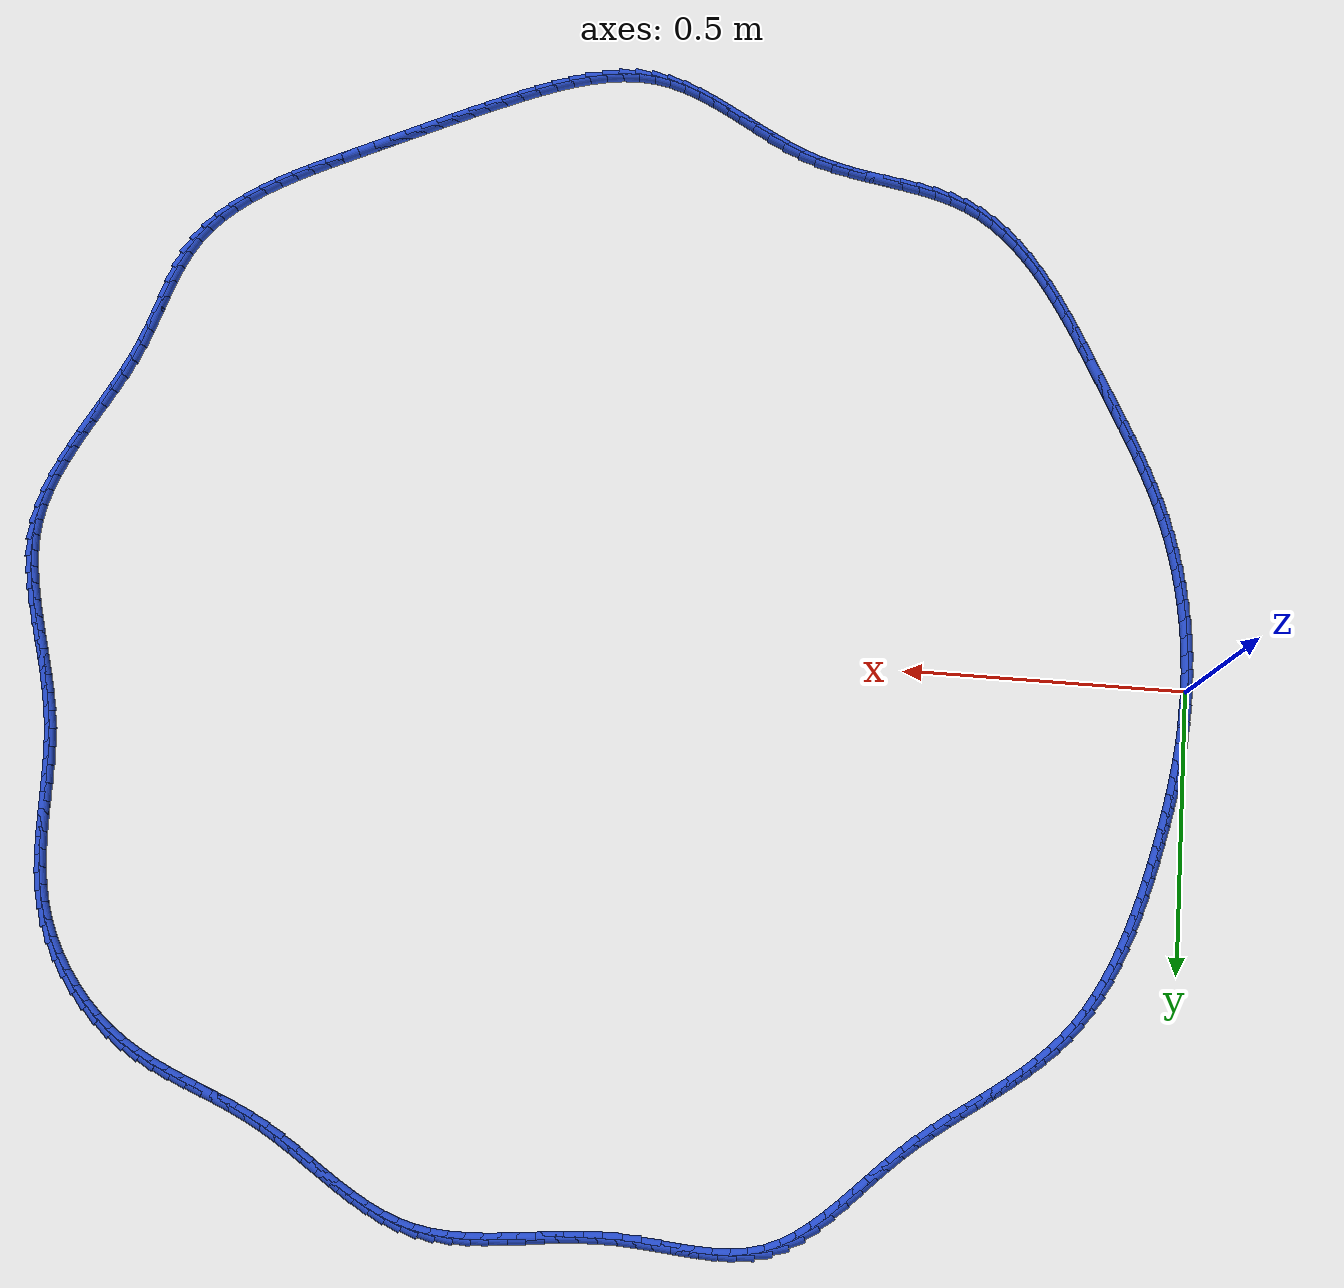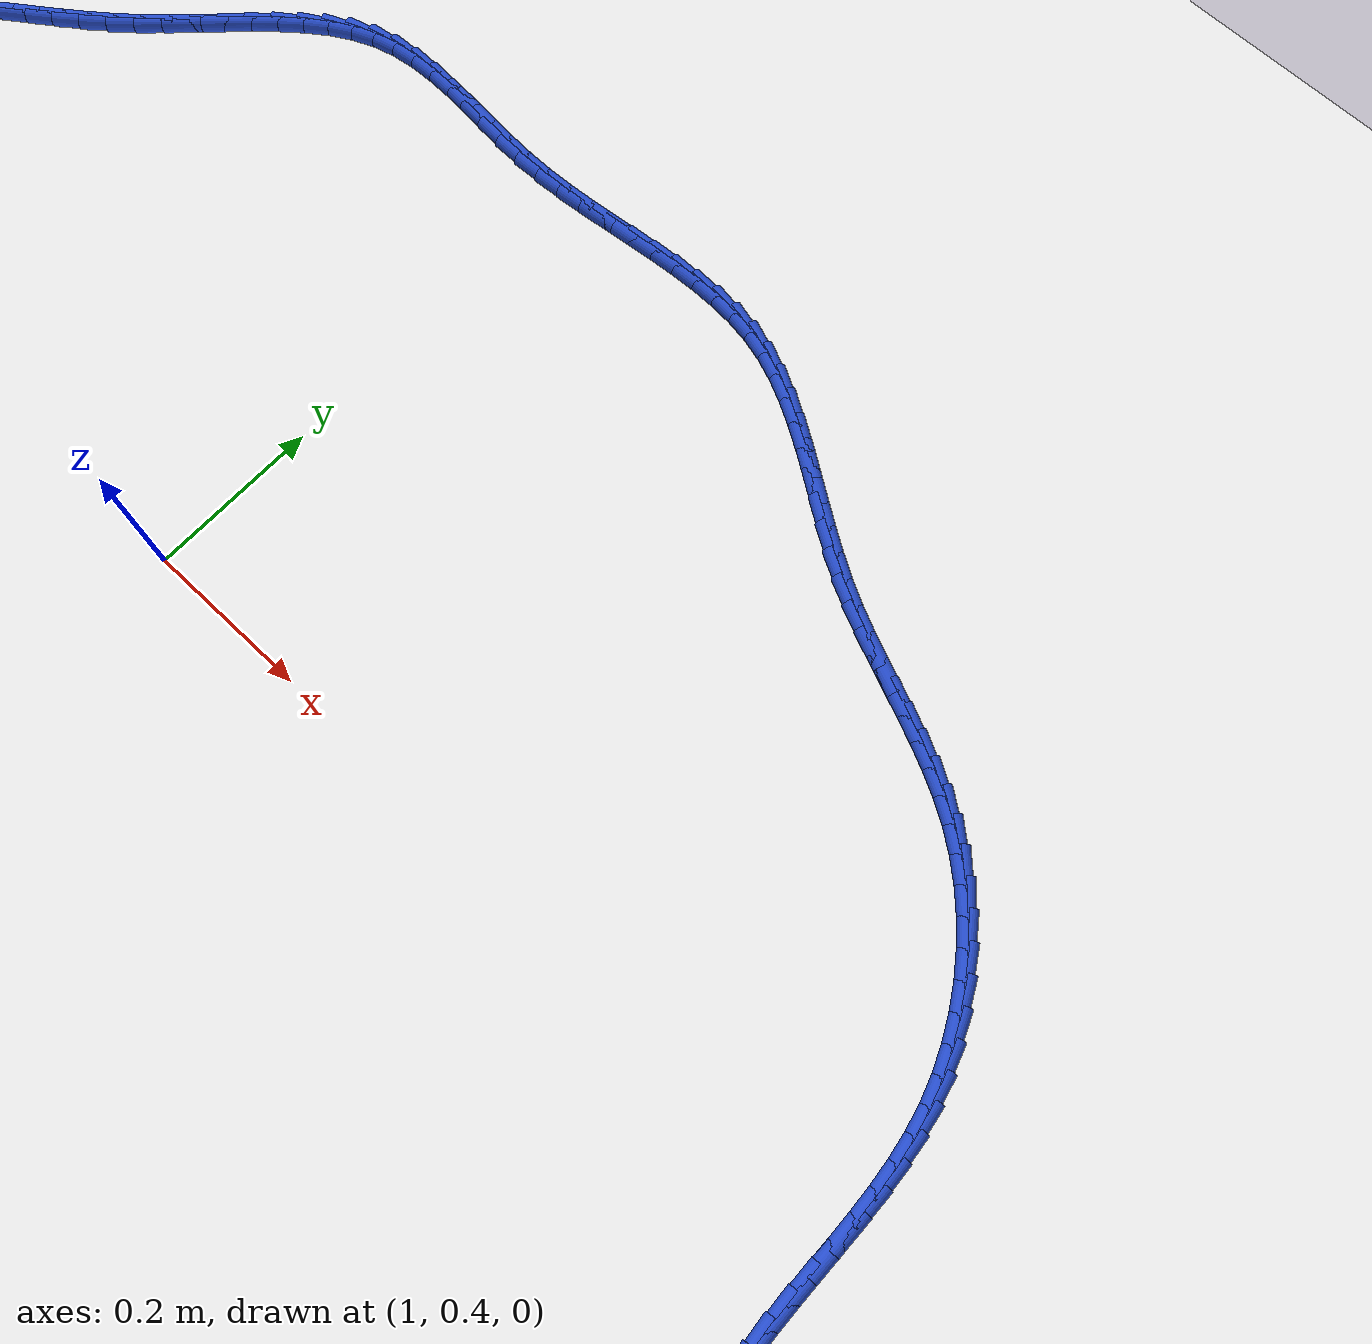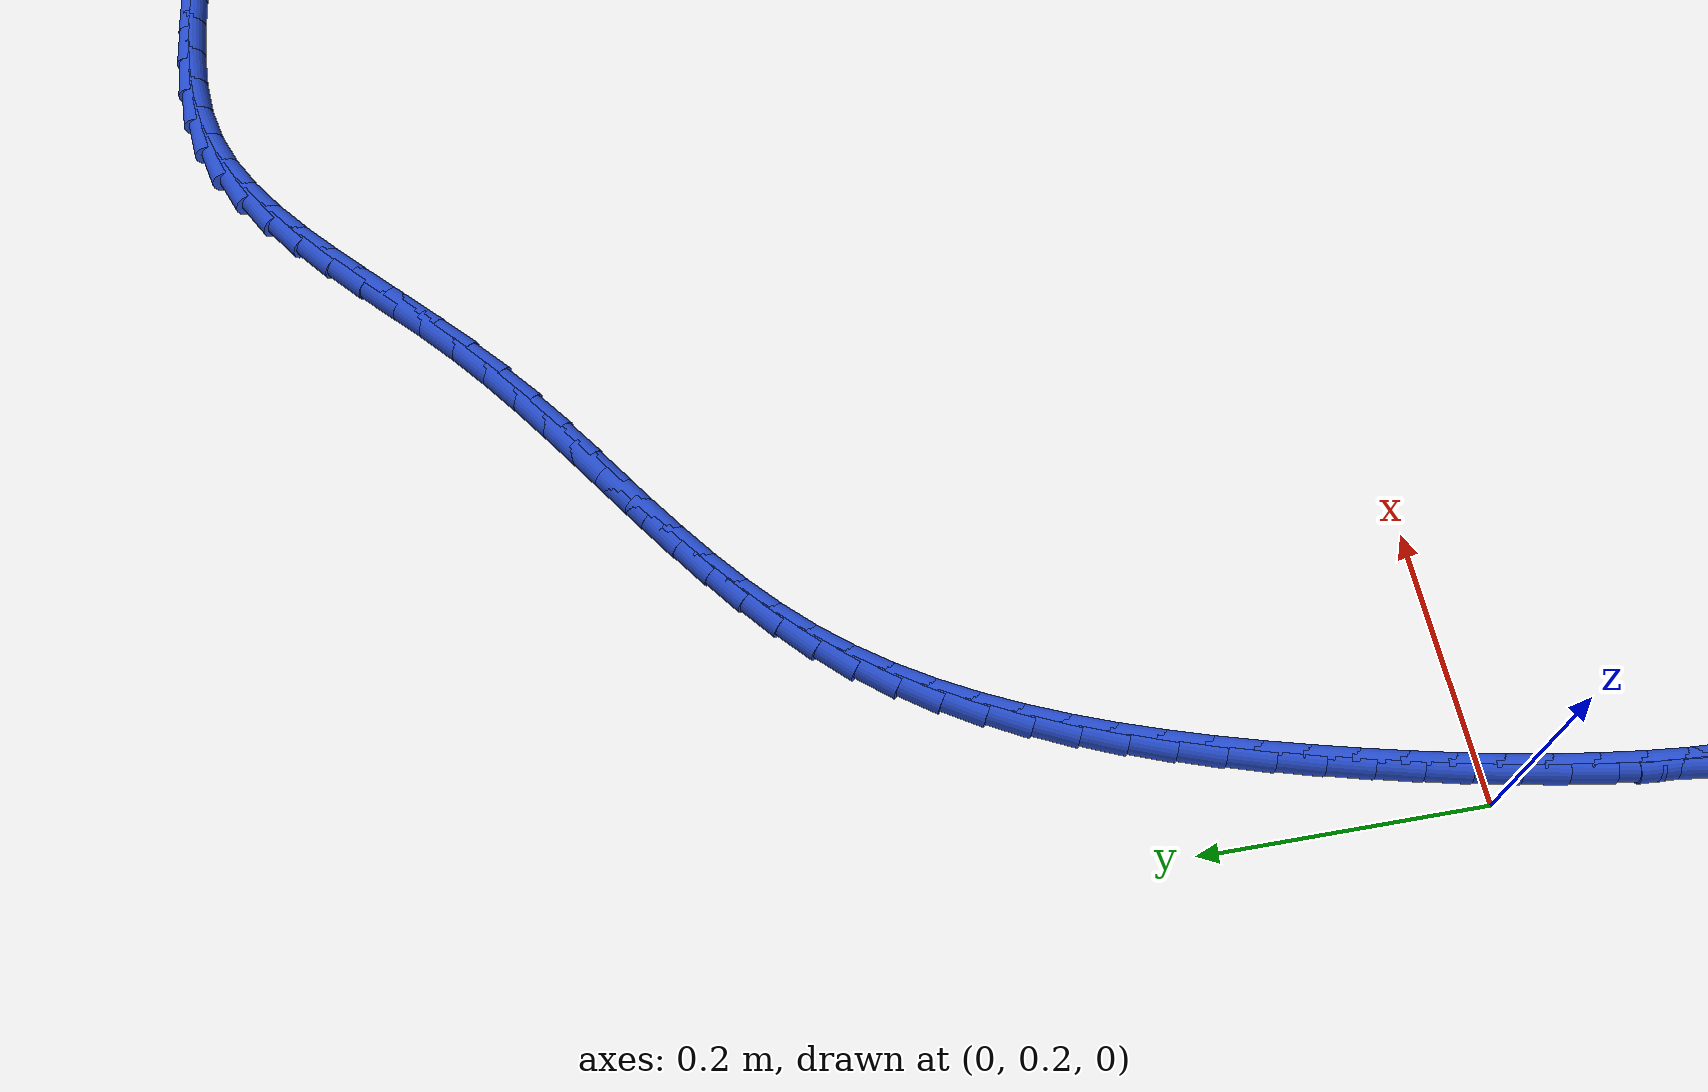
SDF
<sdf version="1.6">
 <world name="default">
  <light name="sun" type="directional">
   <pose>0 0 10 0 -0 0</pose>
   <diffuse>0.8 0.8 0.8 1</diffuse>
   <specular>0.2 0.2 0.2 1</specular>
   <attenuation>
    <range>1000</range>
    <constant>0.9</constant>
    <linear>0.01</linear>
    <quadratic>0.001</quadratic>
   </attenuation>
   <direction>-0.5 0.1 -0.9</direction>
  </light>
  <model name="ground_plane">
   <static>1</static>
   <link name="link">
    <collision name="collision">
     <geometry><plane><normal>0 0 1</normal><size>100 100</size></plane></geometry>
     <surface><friction><ode><mu>100</mu><mu2>50</mu2></ode></friction></surface>
    </collision>
    <visual name="visual">
     <cast_shadows>0</cast_shadows>
     <geometry><plane><normal>0 0 1</normal><size>100 100</size></plane></geometry>
     <material>
      <script><uri>file://media/materials/scripts/gazebo.material</uri><name>Gazebo/WhiteGlow</name></script>
     </material>
    </visual>
   </link>
  </model>
  <gravity>0 0 -9.8</gravity>
  <magnetic_field>6e-06 2.3e-05 -4.2e-05</magnetic_field>
  <atmosphere type="adiabatic"/>
  <physics name="default_physics" default="0" type="ode">
   <max_step_size>0.001</max_step_size>
   <real_time_factor>1</real_time_factor>
   <real_time_update_rate>1000</real_time_update_rate>
  </physics>
  <scene><ambient>0.4 0.4 0.4 1</ambient><background>0.7 0.7 0.7 1</background><shadows>1</shadows></scene>
  <spherical_coordinates>
   <surface_model>EARTH_WGS84</surface_model>
   <latitude_deg>0</latitude_deg>
   <longitude_deg>0</longitude_deg>
   <elevation>0</elevation>
   <heading_deg>0</heading_deg>
  </spherical_coordinates>
  <model name="line">
   <link name="link_0">
    <pose>-3.469446951953614e-18 -6.938893903907228e-18 0.01 0 1.57 1.5374632616049688</pose>
    <collision name="collision">
     <geometry><cylinder><radius>0.01</radius><length>0.08</length></cylinder></geometry>
    </collision>
    <visual name="visual">
     <material>
      <script><name>Gazebo/Blue</name><uri>file://media/materials/scripts/gazebo.material</uri></script>
     </material>
     <geometry><cylinder><radius>0.01</radius><length>0.08</length></cylinder></geometry>
    </visual>
   </link>
   <link name="link_1">
    <pose>0.0010424125092274408 0.03126104371721876 0.01 0 1.57 1.5046778550741806</pose>
    <collision name="collision">
     <geometry><cylinder><radius>0.01</radius><length>0.08</length></cylinder></geometry>
    </collision>
    <visual name="visual">
     <material>
      <script><name>Gazebo/Blue</name><uri>file://media/materials/scripts/gazebo.material</uri></script>
     </material>
     <geometry><cylinder><radius>0.01</radius><length>0.08</length></cylinder></geometry>
    </visual>
   </link>
   <link name="link_2">
    <pose>0.0031026062292826813 0.062374749781334705 0.01 0 1.57 1.473939460340135</pose>
    <collision name="collision">
     <geometry><cylinder><radius>0.01</radius><length>0.08</length></cylinder></geometry>
    </collision>
    <visual name="visual">
     <material>
      <script><name>Gazebo/Blue</name><uri>file://media/materials/scripts/gazebo.material</uri></script>
     </material>
     <geometry><cylinder><radius>0.01</radius><length>0.08</length></cylinder></geometry>
    </visual>
   </link>
   <link name="link_3">
    <pose>0.0061145369325686615 0.09337416527451323 0.01 0 1.57 1.445395270978295</pose>
    <collision name="collision">
     <geometry><cylinder><radius>0.01</radius><length>0.08</length></cylinder></geometry>
    </collision>
    <visual name="visual">
     <material>
      <script><name>Gazebo/Blue</name><uri>file://media/materials/scripts/gazebo.material</uri></script>
     </material>
     <geometry><cylinder><radius>0.01</radius><length>0.08</length></cylinder></geometry>
    </visual>
   </link>
   <link name="link_4">
    <pose>0.010012160391488337 0.12429233727891978 0.01 0 1.57 1.419158370432345</pose>
    <collision name="collision">
     <geometry><cylinder><radius>0.01</radius><length>0.08</length></cylinder></geometry>
    </collision>
    <visual name="visual">
     <material>
      <script><name>Gazebo/Blue</name><uri>file://media/materials/scripts/gazebo.material</uri></script>
     </material>
     <geometry><cylinder><radius>0.01</radius><length>0.08</length></cylinder></geometry>
    </visual>
   </link>
   <link name="link_5">
    <pose>0.014729432378444648 0.15516231287671972 0.01 0 1.57 1.3953099632550863</pose>
    <collision name="collision">
     <geometry><cylinder><radius>0.01</radius><length>0.08</length></cylinder></geometry>
    </collision>
    <visual name="visual">
     <material>
      <script><name>Gazebo/Blue</name><uri>file://media/materials/scripts/gazebo.material</uri></script>
     </material>
     <geometry><cylinder><radius>0.01</radius><length>0.08</length></cylinder></geometry>
    </visual>
   </link>
   <link name="link_6">
    <pose>0.020200308665840556 0.18601713915007853 0.01 0 1.57 1.373902518697268</pose>
    <collision name="collision">
     <geometry><cylinder><radius>0.01</radius><length>0.08</length></cylinder></geometry>
    </collision>
    <visual name="visual">
     <material>
      <script><name>Gazebo/Blue</name><uri>file://media/materials/scripts/gazebo.material</uri></script>
     </material>
     <geometry><cylinder><radius>0.01</radius><length>0.08</length></cylinder></geometry>
    </visual>
   </link>
   <link name="link_7">
    <pose>0.02635874502607901 0.2168898631811616 0.01 0 1.57 1.3549634290930286</pose>
    <collision name="collision">
     <geometry><cylinder><radius>0.01</radius><length>0.08</length></cylinder></geometry>
    </collision>
    <visual name="visual">
     <material>
      <script><name>Gazebo/Blue</name><uri>file://media/materials/scripts/gazebo.material</uri></script>
     </material>
     <geometry><cylinder><radius>0.01</radius><length>0.08</length></cylinder></geometry>
    </visual>
   </link>
   <link name="link_8">
    <pose>0.03313869723156295 0.2478135320521343 0.01 0 1.57 1.338498839523467</pose>
    <collision name="collision">
     <geometry><cylinder><radius>0.01</radius><length>0.08</length></cylinder></geometry>
    </collision>
    <visual name="visual">
     <material>
      <script><name>Gazebo/Blue</name><uri>file://media/materials/scripts/gazebo.material</uri></script>
     </material>
     <geometry><cylinder><radius>0.01</radius><length>0.08</length></cylinder></geometry>
    </visual>
   </link>
   <link name="link_9">
    <pose>0.04047412105469532 0.2788211928451621 0.01 0 1.57 1.32437012627559</pose>
    <collision name="collision">
     <geometry><cylinder><radius>0.01</radius><length>0.08</length></cylinder></geometry>
    </collision>
    <visual name="visual">
     <material>
      <script><name>Gazebo/Blue</name><uri>file://media/materials/scripts/gazebo.material</uri></script>
     </material>
     <geometry><cylinder><radius>0.01</radius><length>0.08</length></cylinder></geometry>
    </visual>
   </link>
   <link name="link_10">
    <pose>0.04830228594703557 0.30994232471106964 0.01 0 1.57 1.309440053932046</pose>
    <collision name="collision">
     <geometry><cylinder><radius>0.01</radius><length>0.08</length></cylinder></geometry>
    </collision>
    <visual name="visual">
     <material>
      <script><name>Gazebo/Blue</name><uri>file://media/materials/scripts/gazebo.material</uri></script>
     </material>
     <geometry><cylinder><radius>0.01</radius><length>0.08</length></cylinder></geometry>
    </visual>
   </link>
   <link name="link_11">
    <pose>0.05664133395840119 0.3411193290045787 0.01 0 1.57 1.2904129745757267</pose>
    <collision name="collision">
     <geometry><cylinder><radius>0.01</radius><length>0.08</length></cylinder></geometry>
    </collision>
    <visual name="visual">
     <material>
      <script><name>Gazebo/Blue</name><uri>file://media/materials/scripts/gazebo.material</uri></script>
     </material>
     <geometry><cylinder><radius>0.01</radius><length>0.08</length></cylinder></geometry>
    </visual>
   </link>
   <link name="link_12">
    <pose>0.06559295540037482 0.37220464832232225 0.01 0 1.57 1.2669774140957082</pose>
    <collision name="collision">
     <geometry><cylinder><radius>0.01</radius><length>0.08</length></cylinder></geometry>
    </collision>
    <visual name="visual">
     <material>
      <script><name>Gazebo/Blue</name><uri>file://media/materials/scripts/gazebo.material</uri></script>
     </material>
     <geometry><cylinder><radius>0.01</radius><length>0.08</length></cylinder></geometry>
    </visual>
   </link>
   <link name="link_13">
    <pose>0.07526268957413251 0.40304658094582246 0.01 0 1.57 1.2388990652985616</pose>
    <collision name="collision">
     <geometry><cylinder><radius>0.01</radius><length>0.08</length></cylinder></geometry>
    </collision>
    <visual name="visual">
     <material>
      <script><name>Gazebo/Blue</name><uri>file://media/materials/scripts/gazebo.material</uri></script>
     </material>
     <geometry><cylinder><radius>0.01</radius><length>0.08</length></cylinder></geometry>
    </visual>
   </link>
   <link name="link_14">
    <pose>0.0857560757808503 0.4334934251566013 0.01 0 1.57 1.2058807477188203</pose>
    <collision name="collision">
     <geometry><cylinder><radius>0.01</radius><length>0.08</length></cylinder></geometry>
    </collision>
    <visual name="visual">
     <material>
      <script><name>Gazebo/Blue</name><uri>file://media/materials/scripts/gazebo.material</uri></script>
     </material>
     <geometry><cylinder><radius>0.01</radius><length>0.08</length></cylinder></geometry>
    </visual>
   </link>
   <link name="link_15">
    <pose>0.0971786533217042 0.46339347923618107 0.01 0 1.57 1.1675735135778058</pose>
    <collision name="collision">
     <geometry><cylinder><radius>0.01</radius><length>0.08</length></cylinder></geometry>
    </collision>
    <visual name="visual">
     <material>
      <script><name>Gazebo/Blue</name><uri>file://media/materials/scripts/gazebo.material</uri></script>
     </material>
     <geometry><cylinder><radius>0.01</radius><length>0.08</length></cylinder></geometry>
    </visual>
   </link>
   <link name="link_16">
    <pose>0.10963596149787026 0.49259504146608374 0.01 0 1.57 1.1235939953996381</pose>
    <collision name="collision">
     <geometry><cylinder><radius>0.01</radius><length>0.08</length></cylinder></geometry>
    </collision>
    <visual name="visual">
     <material>
      <script><name>Gazebo/Blue</name><uri>file://media/materials/scripts/gazebo.material</uri></script>
     </material>
     <geometry><cylinder><radius>0.01</radius><length>0.08</length></cylinder></geometry>
    </visual>
   </link>
   <link name="link_17">
    <pose>0.12323353961052447 0.5209464101278314 0.01 0 1.57 1.0735516022050022</pose>
    <collision name="collision">
     <geometry><cylinder><radius>0.01</radius><length>0.08</length></cylinder></geometry>
    </collision>
    <visual name="visual">
     <material>
      <script><name>Gazebo/Blue</name><uri>file://media/materials/scripts/gazebo.material</uri></script>
     </material>
     <geometry><cylinder><radius>0.01</radius><length>0.08</length></cylinder></geometry>
    </visual>
   </link>
   <link name="link_18">
    <pose>0.13807692696084287 0.5482958835029461 0.01 0 1.57 1.0170895564254745</pose>
    <collision name="collision">
     <geometry><cylinder><radius>0.01</radius><length>0.08</length></cylinder></geometry>
    </collision>
    <visual name="visual">
     <material>
      <script><name>Gazebo/Blue</name><uri>file://media/materials/scripts/gazebo.material</uri></script>
     </material>
     <geometry><cylinder><radius>0.01</radius><length>0.08</length></cylinder></geometry>
    </visual>
   </link>
   <link name="link_19">
    <pose>0.1542716628500016 0.5744917598729503 0.01 0 1.57 0.9539432039357943</pose>
    <collision name="collision">
     <geometry><cylinder><radius>0.01</radius><length>0.08</length></cylinder></geometry>
    </collision>
    <visual name="visual">
     <material>
      <script><name>Gazebo/Blue</name><uri>file://media/materials/scripts/gazebo.material</uri></script>
     </material>
     <geometry><cylinder><radius>0.01</radius><length>0.08</length></cylinder></geometry>
    </visual>
   </link>
   <link name="link_20">
    <pose>0.1719232865791765 0.5993823375193654 0.01 0 1.57 0.8840601311046977</pose>
    <collision name="collision">
     <geometry><cylinder><radius>0.01</radius><length>0.08</length></cylinder></geometry>
    </collision>
    <visual name="visual">
     <material>
      <script><name>Gazebo/Blue</name><uri>file://media/materials/scripts/gazebo.material</uri></script>
     </material>
     <geometry><cylinder><radius>0.01</radius><length>0.08</length></cylinder></geometry>
    </visual>
   </link>
   <link name="link_21">
    <pose>0.1911365075809445 0.6228169876965481 0.01 0 1.57 0.8129370297855333</pose>
    <collision name="collision">
     <geometry><cylinder><radius>0.01</radius><length>0.08</length></cylinder></geometry>
    </collision>
    <visual name="visual">
     <material>
      <script><name>Gazebo/Blue</name><uri>file://media/materials/scripts/gazebo.material</uri></script>
     </material>
     <geometry><cylinder><radius>0.01</radius><length>0.08</length></cylinder></geometry>
    </visual>
   </link>
   <link name="link_22">
    <pose>0.21191631395889213 0.6447740156576184 0.01 0 1.57 0.7515742842364286</pose>
    <collision name="collision">
     <geometry><cylinder><radius>0.01</radius><length>0.08</length></cylinder></geometry>
    </collision>
    <visual name="visual">
     <material>
      <script><name>Gazebo/Blue</name><uri>file://media/materials/scripts/gazebo.material</uri></script>
     </material>
     <geometry><cylinder><radius>0.01</radius><length>0.08</length></cylinder></geometry>
    </visual>
   </link>
   <link name="link_23">
    <pose>0.2340743916555512 0.6654816553404339 0.01 0 1.57 0.7017033571511775</pose>
    <collision name="collision">
     <geometry><cylinder><radius>0.01</radius><length>0.08</length></cylinder></geometry>
    </collision>
    <visual name="visual">
     <material>
      <script><name>Gazebo/Blue</name><uri>file://media/materials/scripts/gazebo.material</uri></script>
     </material>
     <geometry><cylinder><radius>0.01</radius><length>0.08</length></cylinder></geometry>
    </visual>
   </link>
   <link name="link_24">
    <pose>0.2574002691879749 0.6851967889720207 0.01 0 1.57 0.663414064282118</pose>
    <collision name="collision">
     <geometry><cylinder><radius>0.01</radius><length>0.08</length></cylinder></geometry>
    </collision>
    <visual name="visual">
     <material>
      <script><name>Gazebo/Blue</name><uri>file://media/materials/scripts/gazebo.material</uri></script>
     </material>
     <geometry><cylinder><radius>0.01</radius><length>0.08</length></cylinder></geometry>
    </visual>
   </link>
   <link name="link_25">
    <pose>0.2816834750732168 0.7041762987794064 0.01 0 1.57 0.6365156320590385</pose>
    <collision name="collision">
     <geometry><cylinder><radius>0.01</radius><length>0.08</length></cylinder></geometry>
    </collision>
    <visual name="visual">
     <material>
      <script><name>Gazebo/Blue</name><uri>file://media/materials/scripts/gazebo.material</uri></script>
     </material>
     <geometry><cylinder><radius>0.01</radius><length>0.08</length></cylinder></geometry>
    </visual>
   </link>
   <link name="link_26">
    <pose>0.30671353782832955 0.7226770669896165 0.01 0 1.57 0.6206937872995485</pose>
    <collision name="collision">
     <geometry><cylinder><radius>0.01</radius><length>0.08</length></cylinder></geometry>
    </collision>
    <visual name="visual">
     <material>
      <script><name>Gazebo/Blue</name><uri>file://media/materials/scripts/gazebo.material</uri></script>
     </material>
     <geometry><cylinder><radius>0.01</radius><length>0.08</length></cylinder></geometry>
    </visual>
   </link>
   <link name="link_27">
    <pose>0.33227998597036706 0.7409559758296789 0.01 0 1.57 0.6156153061417663</pose>
    <collision name="collision">
     <geometry><cylinder><radius>0.01</radius><length>0.08</length></cylinder></geometry>
    </collision>
    <visual name="visual">
     <material>
      <script><name>Gazebo/Blue</name><uri>file://media/materials/scripts/gazebo.material</uri></script>
     </material>
     <geometry><cylinder><radius>0.01</radius><length>0.08</length></cylinder></geometry>
    </visual>
   </link>
   <link name="link_28">
    <pose>0.35817234801638226 0.7592699075266195 0.01 0 1.57 0.6209832081552575</pose>
    <collision name="collision">
     <geometry><cylinder><radius>0.01</radius><length>0.08</length></cylinder></geometry>
    </collision>
    <visual name="visual">
     <material>
      <script><name>Gazebo/Blue</name><uri>file://media/materials/scripts/gazebo.material</uri></script>
     </material>
     <geometry><cylinder><radius>0.01</radius><length>0.08</length></cylinder></geometry>
    </visual>
   </link>
   <link name="link_29">
    <pose>0.3841801524834282 0.7778757443074652 0.01 0 1.57 0.6365507193358064</pose>
    <collision name="collision">
     <geometry><cylinder><radius>0.01</radius><length>0.08</length></cylinder></geometry>
    </collision>
    <visual name="visual">
     <material>
      <script><name>Gazebo/Blue</name><uri>file://media/materials/scripts/gazebo.material</uri></script>
     </material>
     <geometry><cylinder><radius>0.01</radius><length>0.08</length></cylinder></geometry>
    </visual>
   </link>
   <link name="link_30">
    <pose>0.41009292788855867 0.797030368399243 0.01 0 1.57 0.662101331183834</pose>
    <collision name="collision">
     <geometry><cylinder><radius>0.01</radius><length>0.08</length></cylinder></geometry>
    </collision>
    <visual name="visual">
     <material>
      <script><name>Gazebo/Blue</name><uri>file://media/materials/scripts/gazebo.material</uri></script>
     </material>
     <geometry><cylinder><radius>0.01</radius><length>0.08</length></cylinder></geometry>
    </visual>
   </link>
   <link name="link_31">
    <pose>0.43570020274882626 0.8169906620289791 0.01 0 1.57 0.6974002145431685</pose>
    <collision name="collision">
     <geometry><cylinder><radius>0.01</radius><length>0.08</length></cylinder></geometry>
    </collision>
    <visual name="visual">
     <material>
      <script><name>Gazebo/Blue</name><uri>file://media/materials/scripts/gazebo.material</uri></script>
     </material>
     <geometry><cylinder><radius>0.01</radius><length>0.08</length></cylinder></geometry>
    </visual>
   </link>
   <link name="link_32">
    <pose>0.4607915055812847 0.8380135074237003 0.01 0 1.57 0.7382220612444971</pose>
    <collision name="collision">
     <geometry><cylinder><radius>0.01</radius><length>0.08</length></cylinder></geometry>
    </collision>
    <visual name="visual">
     <material>
      <script><name>Gazebo/Blue</name><uri>file://media/materials/scripts/gazebo.material</uri></script>
     </material>
     <geometry><cylinder><radius>0.01</radius><length>0.08</length></cylinder></geometry>
    </visual>
   </link>
   <link name="link_33">
    <pose>0.48521746118042597 0.8602370857438127 0.01 0 1.57 0.7658696968263236</pose>
    <collision name="collision">
     <geometry><cylinder><radius>0.01</radius><length>0.08</length></cylinder></geometry>
    </collision>
    <visual name="visual">
     <material>
      <script><name>Gazebo/Blue</name><uri>file://media/materials/scripts/gazebo.material</uri></script>
     </material>
     <geometry><cylinder><radius>0.01</radius><length>0.08</length></cylinder></geometry>
    </visual>
   </link>
   <link name="link_34">
    <pose>0.5091233677856777 0.8832270710562445 0.01 0 1.57 0.7753450988576904</pose>
    <collision name="collision">
     <geometry><cylinder><radius>0.01</radius><length>0.08</length></cylinder></geometry>
    </collision>
    <visual name="visual">
     <material>
      <script><name>Gazebo/Blue</name><uri>file://media/materials/scripts/gazebo.material</uri></script>
     </material>
     <geometry><cylinder><radius>0.01</radius><length>0.08</length></cylinder></geometry>
    </visual>
   </link>
   <link name="link_35">
    <pose>0.5327432483784463 0.9063767583248105 0.01 0 1.57 0.7667006292148798</pose>
    <collision name="collision">
     <geometry><cylinder><radius>0.01</radius><length>0.08</length></cylinder></geometry>
    </collision>
    <visual name="visual">
     <material>
      <script><name>Gazebo/Blue</name><uri>file://media/materials/scripts/gazebo.material</uri></script>
     </material>
     <geometry><cylinder><radius>0.01</radius><length>0.08</length></cylinder></geometry>
    </visual>
   </link>
   <link name="link_36">
    <pose>0.5563111437982103 0.9290794078177206 0.01 0 1.57 0.7391506883423902</pose>
    <collision name="collision">
     <geometry><cylinder><radius>0.01</radius><length>0.08</length></cylinder></geometry>
    </collision>
    <visual name="visual">
     <material>
      <script><name>Gazebo/Blue</name><uri>file://media/materials/scripts/gazebo.material</uri></script>
     </material>
     <geometry><cylinder><radius>0.01</radius><length>0.08</length></cylinder></geometry>
    </visual>
   </link>
   <link name="link_37">
    <pose>0.580061094884449 0.950728279803186 0.01 0 1.57 0.6910634474077436</pose>
    <collision name="collision">
     <geometry><cylinder><radius>0.01</radius><length>0.08</length></cylinder></geometry>
    </collision>
    <visual name="visual">
     <material>
      <script><name>Gazebo/Blue</name><uri>file://media/materials/scripts/gazebo.material</uri></script>
     </material>
     <geometry><cylinder><radius>0.01</radius><length>0.08</length></cylinder></geometry>
    </visual>
   </link>
   <link name="link_38">
    <pose>0.6042271424766409 0.9707166345494165 0.01 0 1.57 0.6201227689362638</pose>
    <collision name="collision">
     <geometry><cylinder><radius>0.01</radius><length>0.08</length></cylinder></geometry>
    </collision>
    <visual name="visual">
     <material>
      <script><name>Gazebo/Blue</name><uri>file://media/materials/scripts/gazebo.material</uri></script>
     </material>
     <geometry><cylinder><radius>0.01</radius><length>0.08</length></cylinder></geometry>
    </visual>
   </link>
   <link name="link_39">
    <pose>0.6290433274142645 0.9884377323246231 0.01 0 1.57 0.5238610718079503</pose>
    <collision name="collision">
     <geometry><cylinder><radius>0.01</radius><length>0.08</length></cylinder></geometry>
    </collision>
    <visual name="visual">
     <material>
      <script><name>Gazebo/Blue</name><uri>file://media/materials/scripts/gazebo.material</uri></script>
     </material>
     <geometry><cylinder><radius>0.01</radius><length>0.08</length></cylinder></geometry>
    </visual>
   </link>
   <link name="link_40">
    <pose>0.6547436905367989 1.0032848333970157 0.01 0 1.57 0.4008743291315447</pose>
    <collision name="collision">
     <geometry><cylinder><radius>0.01</radius><length>0.08</length></cylinder></geometry>
    </collision>
    <visual name="visual">
     <material>
      <script><name>Gazebo/Blue</name><uri>file://media/materials/scripts/gazebo.material</uri></script>
     </material>
     <geometry><cylinder><radius>0.01</radius><length>0.08</length></cylinder></geometry>
    </visual>
   </link>
   <link name="link_41">
    <pose>0.6815622726837227 1.014651198034805 0.01 0 1.57 0.25779829616656136</pose>
    <collision name="collision">
     <geometry><cylinder><radius>0.01</radius><length>0.08</length></cylinder></geometry>
    </collision>
    <visual name="visual">
     <material>
      <script><name>Gazebo/Blue</name><uri>file://media/materials/scripts/gazebo.material</uri></script>
     </material>
     <geometry><cylinder><radius>0.01</radius><length>0.08</length></cylinder></geometry>
    </visual>
   </link>
   <link name="link_42">
    <pose>0.7096908434317354 1.022067729035599 0.01 0 1.57 0.13098296952747399</pose>
    <collision name="collision">
     <geometry><cylinder><radius>0.01</radius><length>0.08</length></cylinder></geometry>
    </collision>
    <visual name="visual">
     <material>
      <script><name>Gazebo/Blue</name><uri>file://media/materials/scripts/gazebo.material</uri></script>
     </material>
     <geometry><cylinder><radius>0.01</radius><length>0.08</length></cylinder></geometry>
    </visual>
   </link>
   <link name="link_43">
    <pose>0.7390538048764727 1.0259359238741572 0.01 0 1.57 0.03485881462698105</pose>
    <collision name="collision">
     <geometry><cylinder><radius>0.01</radius><length>0.08</length></cylinder></geometry>
    </collision>
    <visual name="visual">
     <material>
      <script><name>Gazebo/Blue</name><uri>file://media/materials/scripts/gazebo.material</uri></script>
     </material>
     <geometry><cylinder><radius>0.01</radius><length>0.08</length></cylinder></geometry>
    </visual>
   </link>
   <link name="link_44">
    <pose>0.769471328657897 1.0269966723834474 0.01 0 1.57 -0.03210698605639801</pose>
    <collision name="collision">
     <geometry><cylinder><radius>0.01</radius><length>0.08</length></cylinder></geometry>
    </collision>
    <visual name="visual">
     <material>
      <script><name>Gazebo/Blue</name><uri>file://media/materials/scripts/gazebo.material</uri></script>
     </material>
     <geometry><cylinder><radius>0.01</radius><length>0.08</length></cylinder></geometry>
    </visual>
   </link>
   <link name="link_45">
    <pose>0.800763349904306 1.02599163451925 0.01 0 1.57 -0.07268891583874941</pose>
    <collision name="collision">
     <geometry><cylinder><radius>0.01</radius><length>0.08</length></cylinder></geometry>
    </collision>
    <visual name="visual">
     <material>
      <script><name>Gazebo/Blue</name><uri>file://media/materials/scripts/gazebo.material</uri></script>
     </material>
     <geometry><cylinder><radius>0.01</radius><length>0.08</length></cylinder></geometry>
    </visual>
   </link>
   <link name="link_46">
    <pose>0.8327498037439977 1.0236624702373451 0.01 0 1.57 -0.0893478561496461</pose>
    <collision name="collision">
     <geometry><cylinder><radius>0.01</radius><length>0.08</length></cylinder></geometry>
    </collision>
    <visual name="visual">
     <material>
      <script><name>Gazebo/Blue</name><uri>file://media/materials/scripts/gazebo.material</uri></script>
     </material>
     <geometry><cylinder><radius>0.01</radius><length>0.08</length></cylinder></geometry>
    </visual>
   </link>
   <link name="link_47">
    <pose>0.8652506253052693 1.0207508394935123 0.01 0 1.57 -0.08363048422676934</pose>
    <collision name="collision">
     <geometry><cylinder><radius>0.01</radius><length>0.08</length></cylinder></geometry>
    </collision>
    <visual name="visual">
     <material>
      <script><name>Gazebo/Blue</name><uri>file://media/materials/scripts/gazebo.material</uri></script>
     </material>
     <geometry><cylinder><radius>0.01</radius><length>0.08</length></cylinder></geometry>
    </visual>
   </link>
   <link name="link_48">
    <pose>0.8980857497164194 1.0179984022435316 0.01 0 1.57 -0.05606786682696185</pose>
    <collision name="collision">
     <geometry><cylinder><radius>0.01</radius><length>0.08</length></cylinder></geometry>
    </collision>
    <visual name="visual">
     <material>
      <script><name>Gazebo/Blue</name><uri>file://media/materials/scripts/gazebo.material</uri></script>
     </material>
     <geometry><cylinder><radius>0.01</radius><length>0.08</length></cylinder></geometry>
    </visual>
   </link>
   <link name="link_49">
    <pose>0.9310751121057452 1.0161468184431832 0.01 0 1.57 -0.007897198484865387</pose>
    <collision name="collision">
     <geometry><cylinder><radius>0.01</radius><length>0.08</length></cylinder></geometry>
    </collision>
    <visual name="visual">
     <material>
      <script><name>Gazebo/Blue</name><uri>file://media/materials/scripts/gazebo.material</uri></script>
     </material>
     <geometry><cylinder><radius>0.01</radius><length>0.08</length></cylinder></geometry>
    </visual>
   </link>
   <link name="link_50">
    <pose>0.9640439431642798 1.0158864516278208 0.01 0 1.57 0.04108662085748452</pose>
    <collision name="collision">
     <geometry><cylinder><radius>0.01</radius><length>0.08</length></cylinder></geometry>
    </collision>
    <visual name="visual">
     <material>
      <script><name>Gazebo/Blue</name><uri>file://media/materials/scripts/gazebo.material</uri></script>
     </material>
     <geometry><cylinder><radius>0.01</radius><length>0.08</length></cylinder></geometry>
    </visual>
   </link>
   <link name="link_51">
    <pose>0.9968867495333809 1.0172366113861018 0.01 0 1.57 0.07666247405584407</pose>
    <collision name="collision">
     <geometry><cylinder><radius>0.01</radius><length>0.08</length></cylinder></geometry>
    </collision>
    <visual name="visual">
     <material>
      <script><name>Gazebo/Blue</name><uri>file://media/materials/scripts/gazebo.material</uri></script>
     </material>
     <geometry><cylinder><radius>0.01</radius><length>0.08</length></cylinder></geometry>
    </visual>
   </link>
   <link name="link_52">
    <pose>1.0295466909963629 1.0197453199006765 0.01 0 1.57 0.0985502799877787</pose>
    <collision name="collision">
     <geometry><cylinder><radius>0.01</radius><length>0.08</length></cylinder></geometry>
    </collision>
    <visual name="visual">
     <material>
      <script><name>Gazebo/Blue</name><uri>file://media/materials/scripts/gazebo.material</uri></script>
     </material>
     <geometry><cylinder><radius>0.01</radius><length>0.08</length></cylinder></geometry>
    </visual>
   </link>
   <link name="link_53">
    <pose>1.0619679361933965 1.022950826880873 0.01 0 1.57 0.10668664544577708</pose>
    <collision name="collision">
     <geometry><cylinder><radius>0.01</radius><length>0.08</length></cylinder></geometry>
    </collision>
    <visual name="visual">
     <material>
      <script><name>Gazebo/Blue</name><uri>file://media/materials/scripts/gazebo.material</uri></script>
     </material>
     <geometry><cylinder><radius>0.01</radius><length>0.08</length></cylinder></geometry>
    </visual>
   </link>
   <link name="link_54">
    <pose>1.0940946537646532 1.0263913820360195 0.01 0 1.57 0.10079699240235727</pose>
    <collision name="collision">
     <geometry><cylinder><radius>0.01</radius><length>0.08</length></cylinder></geometry>
    </collision>
    <visual name="visual">
     <material>
      <script><name>Gazebo/Blue</name><uri>file://media/materials/scripts/gazebo.material</uri></script>
     </material>
     <geometry><cylinder><radius>0.01</radius><length>0.08</length></cylinder></geometry>
    </visual>
   </link>
   <link name="link_55">
    <pose>1.125871012350304 1.0296052350754445 0.01 0 1.57 0.08033001967737259</pose>
    <collision name="collision">
     <geometry><cylinder><radius>0.01</radius><length>0.08</length></cylinder></geometry>
    </collision>
    <visual name="visual">
     <material>
      <script><name>Gazebo/Blue</name><uri>file://media/materials/scripts/gazebo.material</uri></script>
     </material>
     <geometry><cylinder><radius>0.01</radius><length>0.08</length></cylinder></geometry>
    </visual>
   </link>
   <link name="link_56">
    <pose>1.1572411805905212 1.0321306357084772 0.01 0 1.57 0.04446373219891118</pose>
    <collision name="collision">
     <geometry><cylinder><radius>0.01</radius><length>0.08</length></cylinder></geometry>
    </collision>
    <visual name="visual">
     <material>
      <script><name>Gazebo/Blue</name><uri>file://media/materials/scripts/gazebo.material</uri></script>
     </material>
     <geometry><cylinder><radius>0.01</radius><length>0.08</length></cylinder></geometry>
    </visual>
   </link>
   <link name="link_57">
    <pose>1.1881493271254748 1.0335058336444454 0.01 0 1.57 -0.007790324976418928</pose>
    <collision name="collision">
     <geometry><cylinder><radius>0.01</radius><length>0.08</length></cylinder></geometry>
    </collision>
    <visual name="visual">
     <material>
      <script><name>Gazebo/Blue</name><uri>file://media/materials/scripts/gazebo.material</uri></script>
     </material>
     <geometry><cylinder><radius>0.01</radius><length>0.08</length></cylinder></geometry>
    </visual>
   </link>
   <link name="link_58">
    <pose>1.2185396205953376 1.0332690785926784 0.01 0 1.57 -0.07733443137409492</pose>
    <collision name="collision">
     <geometry><cylinder><radius>0.01</radius><length>0.08</length></cylinder></geometry>
    </collision>
    <visual name="visual">
     <material>
      <script><name>Gazebo/Blue</name><uri>file://media/materials/scripts/gazebo.material</uri></script>
     </material>
     <geometry><cylinder><radius>0.01</radius><length>0.08</length></cylinder></geometry>
    </visual>
   </link>
   <link name="link_59">
    <pose>1.24835622964028 1.0309586202625043 0.01 0 1.57 -0.16452844738512007</pose>
    <collision name="collision">
     <geometry><cylinder><radius>0.01</radius><length>0.08</length></cylinder></geometry>
    </collision>
    <visual name="visual">
     <material>
      <script><name>Gazebo/Blue</name><uri>file://media/materials/scripts/gazebo.material</uri></script>
     </material>
     <geometry><cylinder><radius>0.01</radius><length>0.08</length></cylinder></geometry>
    </visual>
   </link>
   <link name="link_60">
    <pose>1.2775433229004738 1.0261127083632515 0.01 0 1.57 -0.267700751961531</pose>
    <collision name="collision">
     <geometry><cylinder><radius>0.01</radius><length>0.08</length></cylinder></geometry>
    </collision>
    <visual name="visual">
     <material>
      <script><name>Gazebo/Blue</name><uri>file://media/materials/scripts/gazebo.material</uri></script>
     </material>
     <geometry><cylinder><radius>0.01</radius><length>0.08</length></cylinder></geometry>
    </visual>
   </link>
   <link name="link_61">
    <pose>1.3060499091277775 1.0182937979865905 0.01 0 1.57 -0.3681553916015632</pose>
    <collision name="collision">
     <geometry><cylinder><radius>0.01</radius><length>0.08</length></cylinder></geometry>
    </collision>
    <visual name="visual">
     <material>
      <script><name>Gazebo/Blue</name><uri>file://media/materials/scripts/gazebo.material</uri></script>
     </material>
     <geometry><cylinder><radius>0.01</radius><length>0.08</length></cylinder></geometry>
    </visual>
   </link>
   <link name="link_62">
    <pose>1.3339206801874217 1.0075428551537553 0.01 0 1.57 -0.449506511914954</pose>
    <collision name="collision">
     <geometry><cylinder><radius>0.01</radius><length>0.08</length></cylinder></geometry>
    </collision>
    <visual name="visual">
     <material>
      <script><name>Gazebo/Blue</name><uri>file://media/materials/scripts/gazebo.material</uri></script>
     </material>
     <geometry><cylinder><radius>0.01</radius><length>0.08</length></cylinder></geometry>
    </visual>
   </link>
   <link name="link_63">
    <pose>1.3612880532535867 0.9943395598622773 0.01 0 1.57 -0.5116138458323856</pose>
    <collision name="collision">
     <geometry><cylinder><radius>0.01</radius><length>0.08</length></cylinder></geometry>
    </collision>
    <visual name="visual">
     <material>
      <script><name>Gazebo/Blue</name><uri>file://media/materials/scripts/gazebo.material</uri></script>
     </material>
     <geometry><cylinder><radius>0.01</radius><length>0.08</length></cylinder></geometry>
    </visual>
   </link>
   <link name="link_64">
    <pose>1.3882876902885875 0.9791798192842922 0.01 0 1.57 -0.5556536244174888</pose>
    <collision name="collision">
     <geometry><cylinder><radius>0.01</radius><length>0.08</length></cylinder></geometry>
    </collision>
    <visual name="visual">
     <material>
      <script><name>Gazebo/Blue</name><uri>file://media/materials/scripts/gazebo.material</uri></script>
     </material>
     <geometry><cylinder><radius>0.01</radius><length>0.08</length></cylinder></geometry>
    </visual>
   </link>
   <link name="link_65">
    <pose>1.4150552532547411 0.9625595405919359 0.01 0 1.57 -0.5829014485841069</pose>
    <collision name="collision">
     <geometry><cylinder><radius>0.01</radius><length>0.08</length></cylinder></geometry>
    </collision>
    <visual name="visual">
     <material>
      <script><name>Gazebo/Blue</name><uri>file://media/materials/scripts/gazebo.material</uri></script>
     </material>
     <geometry><cylinder><radius>0.01</radius><length>0.08</length></cylinder></geometry>
    </visual>
   </link>
   <link name="link_66">
    <pose>1.4417264041143634 0.9449746309573438 0.01 0 1.57 -0.5943695902177217</pose>
    <collision name="collision">
     <geometry><cylinder><radius>0.01</radius><length>0.08</length></cylinder></geometry>
    </collision>
    <visual name="visual">
     <material>
      <script><name>Gazebo/Blue</name><uri>file://media/materials/scripts/gazebo.material</uri></script>
     </material>
     <geometry><cylinder><radius>0.01</radius><length>0.08</length></cylinder></geometry>
    </visual>
   </link>
   <link name="link_67">
    <pose>1.46843680482977 0.9269209975526518 0.01 0 1.57 -0.5906478549886461</pose>
    <collision name="collision">
     <geometry><cylinder><radius>0.01</radius><length>0.08</length></cylinder></geometry>
    </collision>
    <visual name="visual">
     <material>
      <script><name>Gazebo/Blue</name><uri>file://media/materials/scripts/gazebo.material</uri></script>
     </material>
     <geometry><cylinder><radius>0.01</radius><length>0.08</length></cylinder></geometry>
    </visual>
   </link>
   <link name="link_68">
    <pose>1.4953221173632785 0.9088945475499962 0.01 0 1.57 -0.571865195946741</pose>
    <collision name="collision">
     <geometry><cylinder><radius>0.01</radius><length>0.08</length></cylinder></geometry>
    </collision>
    <visual name="visual">
     <material>
      <script><name>Gazebo/Blue</name><uri>file://media/materials/scripts/gazebo.material</uri></script>
     </material>
     <geometry><cylinder><radius>0.01</radius><length>0.08</length></cylinder></geometry>
    </visual>
   </link>
   <link name="link_69">
    <pose>1.5225180036772035 0.8913911881215115 0.01 0 1.57 -0.5377308793178665</pose>
    <collision name="collision">
     <geometry><cylinder><radius>0.01</radius><length>0.08</length></cylinder></geometry>
    </collision>
    <visual name="visual">
     <material>
      <script><name>Gazebo/Blue</name><uri>file://media/materials/scripts/gazebo.material</uri></script>
     </material>
     <geometry><cylinder><radius>0.01</radius><length>0.08</length></cylinder></geometry>
    </visual>
   </link>
   <link name="link_70">
    <pose>1.550160125733862 0.8749068264393347 0.01 0 1.57 -0.4888886992285748</pose>
    <collision name="collision">
     <geometry><cylinder><radius>0.01</radius><length>0.08</length></cylinder></geometry>
    </collision>
    <visual name="visual">
     <material>
      <script><name>Gazebo/Blue</name><uri>file://media/materials/scripts/gazebo.material</uri></script>
     </material>
     <geometry><cylinder><radius>0.01</radius><length>0.08</length></cylinder></geometry>
    </visual>
   </link>
   <link name="link_71">
    <pose>1.5783706556135721 0.8598999100109556 0.01 0 1.57 -0.4421092545885649</pose>
    <collision name="collision">
     <geometry><cylinder><radius>0.01</radius><length>0.08</length></cylinder></geometry>
    </collision>
    <visual name="visual">
     <material>
      <script><name>Gazebo/Blue</name><uri>file://media/materials/scripts/gazebo.material</uri></script>
     </material>
     <geometry><cylinder><radius>0.01</radius><length>0.08</length></cylinder></geometry>
    </visual>
   </link>
   <link name="link_72">
    <pose>1.6070842092671767 0.8463080671318283 0.01 0 1.57 -0.41030129178061026</pose>
    <collision name="collision">
     <geometry><cylinder><radius>0.01</radius><length>0.08</length></cylinder></geometry>
    </collision>
    <visual name="visual">
     <material>
      <script><name>Gazebo/Blue</name><uri>file://media/materials/scripts/gazebo.material</uri></script>
     </material>
     <geometry><cylinder><radius>0.01</radius><length>0.08</length></cylinder></geometry>
    </visual>
   </link>
   <link name="link_73">
    <pose>1.636097999177643 0.8336873743663606 0.01 0 1.57 -0.39402555693082025</pose>
    <collision name="collision">
     <geometry><cylinder><radius>0.01</radius><length>0.08</length></cylinder></geometry>
    </collision>
    <visual name="visual">
     <material>
      <script><name>Gazebo/Blue</name><uri>file://media/materials/scripts/gazebo.material</uri></script>
     </material>
     <geometry><cylinder><radius>0.01</radius><length>0.08</length></cylinder></geometry>
    </visual>
   </link>
   <link name="link_74">
    <pose>1.6652060838992189 0.8215851502251763 0.01 0 1.57 -0.3934559239815299</pose>
    <collision name="collision">
     <geometry><cylinder><radius>0.01</radius><length>0.08</length></cylinder></geometry>
    </collision>
    <visual name="visual">
     <material>
      <script><name>Gazebo/Blue</name><uri>file://media/materials/scripts/gazebo.material</uri></script>
     </material>
     <geometry><cylinder><radius>0.01</radius><length>0.08</length></cylinder></geometry>
    </visual>
   </link>
   <link name="link_75">
    <pose>1.694202521986154 0.8095487132188978 0.01 0 1.57 -0.4087853971269708</pose>
    <collision name="collision">
     <geometry><cylinder><radius>0.01</radius><length>0.08</length></cylinder></geometry>
    </collision>
    <visual name="visual">
     <material>
      <script><name>Gazebo/Blue</name><uri>file://media/materials/scripts/gazebo.material</uri></script>
     </material>
     <geometry><cylinder><radius>0.01</radius><length>0.08</length></cylinder></geometry>
    </visual>
   </link>
   <link name="link_76">
    <pose>1.7228813719926988 0.797125381858149 0.01 0 1.57 -0.44023054530474576</pose>
    <collision name="collision">
     <geometry><cylinder><radius>0.01</radius><length>0.08</length></cylinder></geometry>
    </collision>
    <visual name="visual">
     <material>
      <script><name>Gazebo/Blue</name><uri>file://media/materials/scripts/gazebo.material</uri></script>
     </material>
     <geometry><cylinder><radius>0.01</radius><length>0.08</length></cylinder></geometry>
    </visual>
   </link>
   <link name="link_77">
    <pose>1.7510366924731 0.7838624746535532 0.01 0 1.57 -0.4879124852618369</pose>
    <collision name="collision">
     <geometry><cylinder><radius>0.01</radius><length>0.08</length></cylinder></geometry>
    </collision>
    <visual name="visual">
     <material>
      <script><name>Gazebo/Blue</name><uri>file://media/materials/scripts/gazebo.material</uri></script>
     </material>
     <geometry><cylinder><radius>0.01</radius><length>0.08</length></cylinder></geometry>
    </visual>
   </link>
   <link name="link_78">
    <pose>1.7784625419816082 0.7693073101157335 0.01 0 1.57 -0.5516083225927558</pose>
    <collision name="collision">
     <geometry><cylinder><radius>0.01</radius><length>0.08</length></cylinder></geometry>
    </collision>
    <visual name="visual">
     <material>
      <script><name>Gazebo/Blue</name><uri>file://media/materials/scripts/gazebo.material</uri></script>
     </material>
     <geometry><cylinder><radius>0.01</radius><length>0.08</length></cylinder></geometry>
    </visual>
   </link>
   <link name="link_79">
    <pose>1.8049529790724723 0.7530072067553129 0.01 0 1.57 -0.6297407860938478</pose>
    <collision name="collision">
     <geometry><cylinder><radius>0.01</radius><length>0.08</length></cylinder></geometry>
    </collision>
    <visual name="visual">
     <material>
      <script><name>Gazebo/Blue</name><uri>file://media/materials/scripts/gazebo.material</uri></script>
     </material>
     <geometry><cylinder><radius>0.01</radius><length>0.08</length></cylinder></geometry>
    </visual>
   </link>
   <link name="link_80">
    <pose>1.8303031447447817 0.7345340900482956 0.01 0 1.57 -0.7113617040343441</pose>
    <collision name="collision">
     <geometry><cylinder><radius>0.01</radius><length>0.08</length></cylinder></geometry>
    </collision>
    <visual name="visual">
     <material>
      <script><name>Gazebo/Blue</name><uri>file://media/materials/scripts/gazebo.material</uri></script>
     </material>
     <geometry><cylinder><radius>0.01</radius><length>0.08</length></cylinder></geometry>
    </visual>
   </link>
   <link name="link_81">
    <pose>1.8543244669380998 0.7138301326788152 0.01 0 1.57 -0.7896009369477454</pose>
    <collision name="collision">
     <geometry><cylinder><radius>0.01</radius><length>0.08</length></cylinder></geometry>
    </collision>
    <visual name="visual">
     <material>
      <script><name>Gazebo/Blue</name><uri>file://media/materials/scripts/gazebo.material</uri></script>
     </material>
     <geometry><cylinder><radius>0.01</radius><length>0.08</length></cylinder></geometry>
    </visual>
   </link>
   <link name="link_82">
    <pose>1.8768409576859373 0.6911235785952462 0.01 0 1.57 -0.865507322533157</pose>
    <collision name="collision">
     <geometry><cylinder><radius>0.01</radius><length>0.08</length></cylinder></geometry>
    </collision>
    <visual name="visual">
     <material>
      <script><name>Gazebo/Blue</name><uri>file://media/materials/scripts/gazebo.material</uri></script>
     </material>
     <geometry><cylinder><radius>0.01</radius><length>0.08</length></cylinder></geometry>
    </visual>
   </link>
   <link name="link_83">
    <pose>1.8976769554184512 0.6666500916445659 0.01 0 1.57 -0.940309605896096</pose>
    <collision name="collision">
     <geometry><cylinder><radius>0.01</radius><length>0.08</length></cylinder></geometry>
    </collision>
    <visual name="visual">
     <material>
      <script><name>Gazebo/Blue</name><uri>file://media/materials/scripts/gazebo.material</uri></script>
     </material>
     <geometry><cylinder><radius>0.01</radius><length>0.08</length></cylinder></geometry>
    </visual>
   </link>
   <link name="link_84">
    <pose>1.9166567985657992 0.6406453356737518 0.01 0 1.57 -1.015223922532161</pose>
    <collision name="collision">
     <geometry><cylinder><radius>0.01</radius><length>0.08</length></cylinder></geometry>
    </collision>
    <visual name="visual">
     <material>
      <script><name>Gazebo/Blue</name><uri>file://media/materials/scripts/gazebo.material</uri></script>
     </material>
     <geometry><cylinder><radius>0.01</radius><length>0.08</length></cylinder></geometry>
    </visual>
   </link>
   <link name="link_85">
    <pose>1.9336048255581386 0.61334497452978 0.01 0 1.57 -1.0914660131109797</pose>
    <collision name="collision">
     <geometry><cylinder><radius>0.01</radius><length>0.08</length></cylinder></geometry>
    </collision>
    <visual name="visual">
     <material>
      <script><name>Gazebo/Blue</name><uri>file://media/materials/scripts/gazebo.material</uri></script>
     </material>
     <geometry><cylinder><radius>0.01</radius><length>0.08</length></cylinder></geometry>
    </visual>
   </link>
   <link name="link_86">
    <pose>1.9483453748256259 0.5849846720596282 0.01 0 1.57 -1.1702625314178252</pose>
    <collision name="collision">
     <geometry><cylinder><radius>0.01</radius><length>0.08</length></cylinder></geometry>
    </collision>
    <visual name="visual">
     <material>
      <script><name>Gazebo/Blue</name><uri>file://media/materials/scripts/gazebo.material</uri></script>
     </material>
     <geometry><cylinder><radius>0.01</radius><length>0.08</length></cylinder></geometry>
    </visual>
   </link>
   <link name="link_87">
    <pose>1.9607027847984186 0.5558000921102735 0.01 0 1.57 -1.252838558718122</pose>
    <collision name="collision">
     <geometry><cylinder><radius>0.01</radius><length>0.08</length></cylinder></geometry>
    </collision>
    <visual name="visual">
     <material>
      <script><name>Gazebo/Blue</name><uri>file://media/materials/scripts/gazebo.material</uri></script>
     </material>
     <geometry><cylinder><radius>0.01</radius><length>0.08</length></cylinder></geometry>
    </visual>
   </link>
   <link name="link_88">
    <pose>1.9705019249645817 0.526026731783118 0.01 0 1.57 -1.335675847460159</pose>
    <collision name="collision">
     <geometry><cylinder><radius>0.01</radius><length>0.08</length></cylinder></geometry>
    </collision>
    <visual name="visual">
     <material>
      <script><name>Gazebo/Blue</name><uri>file://media/materials/scripts/gazebo.material</uri></script>
     </material>
     <geometry><cylinder><radius>0.01</radius><length>0.08</length></cylinder></geometry>
    </visual>
   </link>
   <link name="link_89">
    <pose>1.9777310873708296 0.4958487755298158 0.01 0 1.57 -1.407115791777056</pose>
    <collision name="collision">
     <geometry><cylinder><radius>0.01</radius><length>0.08</length></cylinder></geometry>
    </collision>
    <visual name="visual">
     <material>
      <script><name>Gazebo/Blue</name><uri>file://media/materials/scripts/gazebo.material</uri></script>
     </material>
     <geometry><cylinder><radius>0.01</radius><length>0.08</length></cylinder></geometry>
    </visual>
   </link>
   <link name="link_90">
    <pose>1.9827720284657326 0.46532686487619696 0.01 0 1.57 -1.4643820053376226</pose>
    <collision name="collision">
     <geometry><cylinder><radius>0.01</radius><length>0.08</length></cylinder></geometry>
    </collision>
    <visual name="visual">
     <material>
      <script><name>Gazebo/Blue</name><uri>file://media/materials/scripts/gazebo.material</uri></script>
     </material>
     <geometry><cylinder><radius>0.01</radius><length>0.08</length></cylinder></geometry>
    </visual>
   </link>
   <link name="link_91">
    <pose>1.9860645213876413 0.43450342482947374 0.01 0 1.57 -1.5070585994974652</pose>
    <collision name="collision">
     <geometry><cylinder><radius>0.01</radius><length>0.08</length></cylinder></geometry>
    </collision>
    <visual name="visual">
     <material>
      <script><name>Gazebo/Blue</name><uri>file://media/materials/scripts/gazebo.material</uri></script>
     </material>
     <geometry><cylinder><radius>0.01</radius><length>0.08</length></cylinder></geometry>
    </visual>
   </link>
   <link name="link_92">
    <pose>1.988048339274905 0.4034208803968582 0.01 0 1.57 -1.5351901790132993</pose>
    <collision name="collision">
     <geometry><cylinder><radius>0.01</radius><length>0.08</length></cylinder></geometry>
    </collision>
    <visual name="visual">
     <material>
      <script><name>Gazebo/Blue</name><uri>file://media/materials/scripts/gazebo.material</uri></script>
     </material>
     <geometry><cylinder><radius>0.01</radius><length>0.08</length></cylinder></geometry>
    </visual>
   </link>
   <link name="link_93">
    <pose>1.989163255265872 0.37212165658556334 0.01 0 1.57 -1.5490104050726161</pose>
    <collision name="collision">
     <geometry><cylinder><radius>0.01</radius><length>0.08</length></cylinder></geometry>
    </collision>
    <visual name="visual">
     <material>
      <script><name>Gazebo/Blue</name><uri>file://media/materials/scripts/gazebo.material</uri></script>
     </material>
     <geometry><cylinder><radius>0.01</radius><length>0.08</length></cylinder></geometry>
    </visual>
   </link>
   <link name="link_94">
    <pose>1.9898490424988946 0.3406481784028014 0.01 0 1.57 -1.5487646181335177</pose>
    <collision name="collision">
     <geometry><cylinder><radius>0.01</radius><length>0.08</length></cylinder></geometry>
    </collision>
    <visual name="visual">
     <material>
      <script><name>Gazebo/Blue</name><uri>file://media/materials/scripts/gazebo.material</uri></script>
     </material>
     <geometry><cylinder><radius>0.01</radius><length>0.08</length></cylinder></geometry>
    </visual>
   </link>
   <link name="link_95">
    <pose>1.99054547411232 0.3090428708557839 0.01 0 1.57 -1.534627864196822</pose>
    <collision name="collision">
     <geometry><cylinder><radius>0.01</radius><length>0.08</length></cylinder></geometry>
    </collision>
    <visual name="visual">
     <material>
      <script><name>Gazebo/Blue</name><uri>file://media/materials/scripts/gazebo.material</uri></script>
     </material>
     <geometry><cylinder><radius>0.01</radius><length>0.08</length></cylinder></geometry>
    </visual>
   </link>
   <link name="link_96">
    <pose>1.9916923232444996 0.2773481589517243 0.01 0 1.57 -1.5067086841990303</pose>
    <collision name="collision">
     <geometry><cylinder><radius>0.01</radius><length>0.08</length></cylinder></geometry>
    </collision>
    <visual name="visual">
     <material>
      <script><name>Gazebo/Blue</name><uri>file://media/materials/scripts/gazebo.material</uri></script>
     </material>
     <geometry><cylinder><radius>0.01</radius><length>0.08</length></cylinder></geometry>
    </visual>
   </link>
   <link name="link_97">
    <pose>1.9937293630337816 0.24560646769783454 0.01 0 1.57 -1.4651314444157175</pose>
    <collision name="collision">
     <geometry><cylinder><radius>0.01</radius><length>0.08</length></cylinder></geometry>
    </collision>
    <visual name="visual">
     <material>
      <script><name>Gazebo/Blue</name><uri>file://media/materials/scripts/gazebo.material</uri></script>
     </material>
     <geometry><cylinder><radius>0.01</radius><length>0.08</length></cylinder></geometry>
    </visual>
   </link>
   <link name="link_98">
    <pose>1.9970963666185169 0.21386022210132635 0.01 0 1.57 -1.411816448238104</pose>
    <collision name="collision">
     <geometry><cylinder><radius>0.01</radius><length>0.08</length></cylinder></geometry>
    </collision>
    <visual name="visual">
     <material>
      <script><name>Gazebo/Blue</name><uri>file://media/materials/scripts/gazebo.material</uri></script>
     </material>
     <geometry><cylinder><radius>0.01</radius><length>0.08</length></cylinder></geometry>
    </visual>
   </link>
   <link name="link_99">
    <pose>2.002180391626226 0.18215104939166274 0.01 0 1.57 -1.3632565244389878</pose>
    <collision name="collision">
     <geometry><cylinder><radius>0.01</radius><length>0.08</length></cylinder></geometry>
    </collision>
    <visual name="visual">
     <material>
      <script><name>Gazebo/Blue</name><uri>file://media/materials/scripts/gazebo.material</uri></script>
     </material>
     <geometry><cylinder><radius>0.01</radius><length>0.08</length></cylinder></geometry>
    </visual>
   </link>
   <link name="link_100">
    <pose>2.0088425539459287 0.15051261738350824 0.01 0 1.57 -1.3283675213449964</pose>
    <collision name="collision">
     <geometry><cylinder><radius>0.01</radius><length>0.08</length></cylinder></geometry>
    </collision>
    <visual name="visual">
     <material>
      <script><name>Gazebo/Blue</name><uri>file://media/materials/scripts/gazebo.material</uri></script>
     </material>
     <geometry><cylinder><radius>0.01</radius><length>0.08</length></cylinder></geometry>
    </visual>
   </link>
   <link name="link_101">
    <pose>2.016641812137867 0.11897402115021839 0.01 0 1.57 -1.3067555460158198</pose>
    <collision name="collision">
     <geometry><cylinder><radius>0.01</radius><length>0.08</length></cylinder></geometry>
    </collision>
    <visual name="visual">
     <material>
      <script><name>Gazebo/Blue</name><uri>file://media/materials/scripts/gazebo.material</uri></script>
     </material>
     <geometry><cylinder><radius>0.01</radius><length>0.08</length></cylinder></geometry>
    </visual>
   </link>
   <link name="link_102">
    <pose>2.025133522817333 0.08756430125459887 0.01 0 1.57 -1.298113600705032</pose>
    <collision name="collision">
     <geometry><cylinder><radius>0.01</radius><length>0.08</length></cylinder></geometry>
    </collision>
    <visual name="visual">
     <material>
      <script><name>Gazebo/Blue</name><uri>file://media/materials/scripts/gazebo.material</uri></script>
     </material>
     <geometry><cylinder><radius>0.01</radius><length>0.08</length></cylinder></geometry>
    </visual>
   </link>
   <link name="link_103">
    <pose>2.0338730425996223 0.05631249825945436 0.01 0 1.57 -1.3024345158557167</pose>
    <collision name="collision">
     <geometry><cylinder><radius>0.01</radius><length>0.08</length></cylinder></geometry>
    </collision>
    <visual name="visual">
     <material>
      <script><name>Gazebo/Blue</name><uri>file://media/materials/scripts/gazebo.material</uri></script>
     </material>
     <geometry><cylinder><radius>0.01</radius><length>0.08</length></cylinder></geometry>
    </visual>
   </link>
   <link name="link_104">
    <pose>2.042415728100027 0.02524765272758992 0.01 0 1.57 -1.3200598947105835</pose>
    <collision name="collision">
     <geometry><cylinder><radius>0.01</radius><length>0.08</length></cylinder></geometry>
    </collision>
    <visual name="visual">
     <material>
      <script><name>Gazebo/Blue</name><uri>file://media/materials/scripts/gazebo.material</uri></script>
     </material>
     <geometry><cylinder><radius>0.01</radius><length>0.08</length></cylinder></geometry>
    </visual>
   </link>
   <link name="link_105">
    <pose>2.0503169359338416 -0.005601194778189499 0.01 0 1.57 -1.3516840085215462</pose>
    <collision name="collision">
     <geometry><cylinder><radius>0.01</radius><length>0.08</length></cylinder></geometry>
    </collision>
    <visual name="visual">
     <material>
      <script><name>Gazebo/Blue</name><uri>file://media/materials/scripts/gazebo.material</uri></script>
     </material>
     <geometry><cylinder><radius>0.01</radius><length>0.08</length></cylinder></geometry>
    </visual>
   </link>
   <link name="link_106">
    <pose>2.0571320227163583 -0.03620500369507955 0.01 0 1.57 -1.3982987244093392</pose>
    <collision name="collision">
     <geometry><cylinder><radius>0.01</radius><length>0.08</length></cylinder></geometry>
    </collision>
    <visual name="visual">
     <material>
      <script><name>Gazebo/Blue</name><uri>file://media/materials/scripts/gazebo.material</uri></script>
     </material>
     <geometry><cylinder><radius>0.01</radius><length>0.08</length></cylinder></geometry>
    </visual>
   </link>
   <link name="link_107">
    <pose>2.0624163450628714 -0.0665347334602738 0.01 0 1.57 -1.4610397844308627</pose>
    <collision name="collision">
     <geometry><cylinder><radius>0.01</radius><length>0.08</length></cylinder></geometry>
    </collision>
    <visual name="visual">
     <material>
      <script><name>Gazebo/Blue</name><uri>file://media/materials/scripts/gazebo.material</uri></script>
     </material>
     <geometry><cylinder><radius>0.01</radius><length>0.08</length></cylinder></geometry>
    </visual>
   </link>
   <link name="link_108">
    <pose>2.065725259588675 -0.09656134351096796 0.01 0 1.57 -1.5408716105940017</pose>
    <collision name="collision">
     <geometry><cylinder><radius>0.01</radius><length>0.08</length></cylinder></geometry>
    </collision>
    <visual name="visual">
     <material>
      <script><name>Gazebo/Blue</name><uri>file://media/materials/scripts/gazebo.material</uri></script>
     </material>
     <geometry><cylinder><radius>0.01</radius><length>0.08</length></cylinder></geometry>
    </visual>
   </link>
   <link name="link_109">
    <pose>2.0666141229090615 -0.12625579328435704 0.01 0 1.57 1.5035805176974115</pose>
    <collision name="collision">
     <geometry><cylinder><radius>0.01</radius><length>0.08</length></cylinder></geometry>
    </collision>
    <visual name="visual">
     <material>
      <script><name>Gazebo/Blue</name><uri>file://media/materials/scripts/gazebo.material</uri></script>
     </material>
     <geometry><cylinder><radius>0.01</radius><length>0.08</length></cylinder></geometry>
    </visual>
   </link>
   <link name="link_110">
    <pose>2.0646394801676204 -0.1555891909315 0.01 0 1.57 1.398622600005185</pose>
    <collision name="collision">
     <geometry><cylinder><radius>0.01</radius><length>0.08</length></cylinder></geometry>
    </collision>
    <visual name="visual">
     <material>
      <script><name>Gazebo/Blue</name><uri>file://media/materials/scripts/gazebo.material</uri></script>
     </material>
     <geometry><cylinder><radius>0.01</radius><length>0.08</length></cylinder></geometry>
    </visual>
   </link>
   <link name="link_111">
    <pose>2.0596010543860084 -0.18456307208426756 0.01 0 1.57 1.3064444803254587</pose>
    <collision name="collision">
     <geometry><cylinder><radius>0.01</radius><length>0.08</length></cylinder></geometry>
    </collision>
    <visual name="visual">
     <material>
      <script><name>Gazebo/Blue</name><uri>file://media/materials/scripts/gazebo.material</uri></script>
     </material>
     <geometry><cylinder><radius>0.01</radius><length>0.08</length></cylinder></geometry>
    </visual>
   </link>
   <link name="link_112">
    <pose>2.051836876047378 -0.21324632776098953 0.01 0 1.57 1.2305268115369385</pose>
    <collision name="collision">
     <geometry><cylinder><radius>0.01</radius><length>0.08</length></cylinder></geometry>
    </collision>
    <visual name="visual">
     <material>
      <script><name>Gazebo/Blue</name><uri>file://media/materials/scripts/gazebo.material</uri></script>
     </material>
     <geometry><cylinder><radius>0.01</radius><length>0.08</length></cylinder></geometry>
    </visual>
   </link>
   <link name="link_113">
    <pose>2.041757157322084 -0.24171688066872987 0.01 0 1.57 1.1706504016050914</pose>
    <collision name="collision">
     <geometry><cylinder><radius>0.01</radius><length>0.08</length></cylinder></geometry>
    </collision>
    <visual name="visual">
     <material>
      <script><name>Gazebo/Blue</name><uri>file://media/materials/scripts/gazebo.material</uri></script>
     </material>
     <geometry><cylinder><radius>0.01</radius><length>0.08</length></cylinder></geometry>
    </visual>
   </link>
   <link name="link_114">
    <pose>2.029772110380477 -0.27005265351455454 0.01 0 1.57 1.1259732683561428</pose>
    <collision name="collision">
     <geometry><cylinder><radius>0.01</radius><length>0.08</length></cylinder></geometry>
    </collision>
    <visual name="visual">
     <material>
      <script><name>Gazebo/Blue</name><uri>file://media/materials/scripts/gazebo.material</uri></script>
     </material>
     <geometry><cylinder><radius>0.01</radius><length>0.08</length></cylinder></geometry>
    </visual>
   </link>
   <link name="link_115">
    <pose>2.0162919473929124 -0.29833156900552904 0.01 0 1.57 1.0954840666529948</pose>
    <collision name="collision">
     <geometry><cylinder><radius>0.01</radius><length>0.08</length></cylinder></geometry>
    </collision>
    <visual name="visual">
     <material>
      <script><name>Gazebo/Blue</name><uri>file://media/materials/scripts/gazebo.material</uri></script>
     </material>
     <geometry><cylinder><radius>0.01</radius><length>0.08</length></cylinder></geometry>
    </visual>
   </link>
   <link name="link_116">
    <pose>2.001726880529743 -0.3266315498487185 0.01 0 1.57 1.0782753619965721</pose>
    <collision name="collision">
     <geometry><cylinder><radius>0.01</radius><length>0.08</length></cylinder></geometry>
    </collision>
    <visual name="visual">
     <material>
      <script><name>Gazebo/Blue</name><uri>file://media/materials/scripts/gazebo.material</uri></script>
     </material>
     <geometry><cylinder><radius>0.01</radius><length>0.08</length></cylinder></geometry>
    </visual>
   </link>
   <link name="link_117">
    <pose>1.986487121961321 -0.35503051875118824 0.01 0 1.57 1.073680204916332</pose>
    <collision name="collision">
     <geometry><cylinder><radius>0.01</radius><length>0.08</length></cylinder></geometry>
    </collision>
    <visual name="visual">
     <material>
      <script><name>Gazebo/Blue</name><uri>file://media/materials/scripts/gazebo.material</uri></script>
     </material>
     <geometry><cylinder><radius>0.01</radius><length>0.08</length></cylinder></geometry>
    </visual>
   </link>
   <link name="link_118">
    <pose>1.970982883858 -0.38360639842000366 0.01 0 1.57 1.0813218192379979</pose>
    <collision name="collision">
     <geometry><cylinder><radius>0.01</radius><length>0.08</length></cylinder></geometry>
    </collision>
    <visual name="visual">
     <material>
      <script><name>Gazebo/Blue</name><uri>file://media/materials/scripts/gazebo.material</uri></script>
     </material>
     <geometry><cylinder><radius>0.01</radius><length>0.08</length></cylinder></geometry>
    </visual>
   </link>
   <link name="link_119">
    <pose>1.9556243783901333 -0.4124371115622307 0.01 0 1.57 1.1011094773205419</pose>
    <collision name="collision">
     <geometry><cylinder><radius>0.01</radius><length>0.08</length></cylinder></geometry>
    </collision>
    <visual name="visual">
     <material>
      <script><name>Gazebo/Blue</name><uri>file://media/materials/scripts/gazebo.material</uri></script>
     </material>
     <geometry><cylinder><radius>0.01</radius><length>0.08</length></cylinder></geometry>
    </visual>
   </link>
   <link name="link_120">
    <pose>1.9408218177280747 -0.4416005808849335 0.01 0 1.57 1.1331940517532462</pose>
    <collision name="collision">
     <geometry><cylinder><radius>0.01</radius><length>0.08</length></cylinder></geometry>
    </collision>
    <visual name="visual">
     <material>
      <script><name>Gazebo/Blue</name><uri>file://media/materials/scripts/gazebo.material</uri></script>
     </material>
     <geometry><cylinder><radius>0.01</radius><length>0.08</length></cylinder></geometry>
    </visual>
   </link>
   <link name="link_121">
    <pose>1.9269854140421763 -0.47117472909517794 0.01 0 1.57 1.1778690087453942</pose>
    <collision name="collision">
     <geometry><cylinder><radius>0.01</radius><length>0.08</length></cylinder></geometry>
    </collision>
    <visual name="visual">
     <material>
      <script><name>Gazebo/Blue</name><uri>file://media/materials/scripts/gazebo.material</uri></script>
     </material>
     <geometry><cylinder><radius>0.01</radius><length>0.08</length></cylinder></geometry>
    </visual>
   </link>
   <link name="link_122">
    <pose>1.9145250341448536 -0.5012373384863553 0.01 0 1.57 1.2270240633169736</pose>
    <collision name="collision">
     <geometry><cylinder><radius>0.01</radius><length>0.08</length></cylinder></geometry>
    </collision>
    <visual name="visual">
     <material>
      <script><name>Gazebo/Blue</name><uri>file://media/materials/scripts/gazebo.material</uri></script>
     </material>
     <geometry><cylinder><radius>0.01</radius><length>0.08</length></cylinder></geometry>
    </visual>
   </link>
   <link name="link_123">
    <pose>1.9035971837021775 -0.5317631812124626 0.01 0 1.57 1.2574699177674902</pose>
    <collision name="collision">
     <geometry><cylinder><radius>0.01</radius><length>0.08</length></cylinder></geometry>
    </collision>
    <visual name="visual">
     <material>
      <script><name>Gazebo/Blue</name><uri>file://media/materials/scripts/gazebo.material</uri></script>
     </material>
     <geometry><cylinder><radius>0.01</radius><length>0.08</length></cylinder></geometry>
    </visual>
   </link>
   <link name="link_124">
    <pose>1.8936572773726028 -0.5624419838178387 0.01 0 1.57 1.2650999844335613</pose>
    <collision name="collision">
     <geometry><cylinder><radius>0.01</radius><length>0.08</length></cylinder></geometry>
    </collision>
    <visual name="visual">
     <material>
      <script><name>Gazebo/Blue</name><uri>file://media/materials/scripts/gazebo.material</uri></script>
     </material>
     <geometry><cylinder><radius>0.01</radius><length>0.08</length></cylinder></geometry>
    </visual>
   </link>
   <link name="link_125">
    <pose>1.8840404693398973 -0.5929145780243941 0.01 0 1.57 1.249362293330336</pose>
    <collision name="collision">
     <geometry><cylinder><radius>0.01</radius><length>0.08</length></cylinder></geometry>
    </collision>
    <visual name="visual">
     <material>
      <script><name>Gazebo/Blue</name><uri>file://media/materials/scripts/gazebo.material</uri></script>
     </material>
     <geometry><cylinder><radius>0.01</radius><length>0.08</length></cylinder></geometry>
    </visual>
   </link>
   <link name="link_126">
    <pose>1.8740819137878313 -0.6228217955540367 0.01 0 1.57 1.2091053496623614</pose>
    <collision name="collision">
     <geometry><cylinder><radius>0.01</radius><length>0.08</length></cylinder></geometry>
    </collision>
    <visual name="visual">
     <material>
      <script><name>Gazebo/Blue</name><uri>file://media/materials/scripts/gazebo.material</uri></script>
     </material>
     <geometry><cylinder><radius>0.01</radius><length>0.08</length></cylinder></geometry>
    </visual>
   </link>
   <link name="link_127">
    <pose>1.8631167649001754 -0.6518044681286776 0.01 0 1.57 1.142788809898979</pose>
    <collision name="collision">
     <geometry><cylinder><radius>0.01</radius><length>0.08</length></cylinder></geometry>
    </collision>
    <visual name="visual">
     <material>
      <script><name>Gazebo/Blue</name><uri>file://media/materials/scripts/gazebo.material</uri></script>
     </material>
     <geometry><cylinder><radius>0.01</radius><length>0.08</length></cylinder></geometry>
    </visual>
   </link>
   <link name="link_128">
    <pose>1.8504801768606975 -0.6795034274702267 0.01 0 1.57 1.0492345519311874</pose>
    <collision name="collision">
     <geometry><cylinder><radius>0.01</radius><length>0.08</length></cylinder></geometry>
    </collision>
    <visual name="visual">
     <material>
      <script><name>Gazebo/Blue</name><uri>file://media/materials/scripts/gazebo.material</uri></script>
     </material>
     <geometry><cylinder><radius>0.01</radius><length>0.08</length></cylinder></geometry>
    </visual>
   </link>
   <link name="link_129">
    <pose>1.8355073611166977 -0.7055595357457469 0.01 0 1.57 0.9366217355337603</pose>
    <collision name="collision">
     <geometry><cylinder><radius>0.01</radius><length>0.08</length></cylinder></geometry>
    </collision>
    <visual name="visual">
     <material>
      <script><name>Gazebo/Blue</name><uri>file://media/materials/scripts/gazebo.material</uri></script>
     </material>
     <geometry><cylinder><radius>0.01</radius><length>0.08</length></cylinder></geometry>
    </visual>
   </link>
   <link name="link_130">
    <pose>1.817735785951005 -0.7297211884959385 0.01 0 1.57 0.8318644804979223</pose>
    <collision name="collision">
     <geometry><cylinder><radius>0.01</radius><length>0.08</length></cylinder></geometry>
    </collision>
    <visual name="visual">
     <material>
      <script><name>Gazebo/Blue</name><uri>file://media/materials/scripts/gazebo.material</uri></script>
     </material>
     <geometry><cylinder><radius>0.01</radius><length>0.08</length></cylinder></geometry>
    </visual>
   </link>
   <link name="link_131">
    <pose>1.79735889259243 -0.7520855407173171 0.01 0 1.57 0.741149634782639</pose>
    <collision name="collision">
     <geometry><cylinder><radius>0.01</radius><length>0.08</length></cylinder></geometry>
    </collision>
    <visual name="visual">
     <material>
      <script><name>Gazebo/Blue</name><uri>file://media/materials/scripts/gazebo.material</uri></script>
     </material>
     <geometry><cylinder><radius>0.01</radius><length>0.08</length></cylinder></geometry>
    </visual>
   </link>
   <link name="link_132">
    <pose>1.774702873210208 -0.7728203267588344 0.01 0 1.57 0.6643931690091314</pose>
    <collision name="collision">
     <geometry><cylinder><radius>0.01</radius><length>0.08</length></cylinder></geometry>
    </collision>
    <visual name="visual">
     <material>
      <script><name>Gazebo/Blue</name><uri>file://media/materials/scripts/gazebo.material</uri></script>
     </material>
     <geometry><cylinder><radius>0.01</radius><length>0.08</length></cylinder></geometry>
    </visual>
   </link>
   <link name="link_133">
    <pose>1.7500939199735759 -0.7920932809694408 0.01 0 1.57 0.6007798519271356</pose>
    <collision name="collision">
     <geometry><cylinder><radius>0.01</radius><length>0.08</length></cylinder></geometry>
    </collision>
    <visual name="visual">
     <material>
      <script><name>Gazebo/Blue</name><uri>file://media/materials/scripts/gazebo.material</uri></script>
     </material>
     <geometry><cylinder><radius>0.01</radius><length>0.08</length></cylinder></geometry>
    </visual>
   </link>
   <link name="link_134">
    <pose>1.7238582250517693 -0.8100721376980875 0.01 0 1.57 0.5492045805692501</pose>
    <collision name="collision">
     <geometry><cylinder><radius>0.01</radius><length>0.08</length></cylinder></geometry>
    </collision>
    <visual name="visual">
     <material>
      <script><name>Gazebo/Blue</name><uri>file://media/materials/scripts/gazebo.material</uri></script>
     </material>
     <geometry><cylinder><radius>0.01</radius><length>0.08</length></cylinder></geometry>
    </visual>
   </link>
   <link name="link_135">
    <pose>1.696321980614024 -0.8269246312937255 0.01 0 1.57 0.5085618356266397</pose>
    <collision name="collision">
     <geometry><cylinder><radius>0.01</radius><length>0.08</length></cylinder></geometry>
    </collision>
    <visual name="visual">
     <material>
      <script><name>Gazebo/Blue</name><uri>file://media/materials/scripts/gazebo.material</uri></script>
     </material>
     <geometry><cylinder><radius>0.01</radius><length>0.08</length></cylinder></geometry>
    </visual>
   </link>
   <link name="link_136">
    <pose>1.6678113788295754 -0.8428184961053059 0.01 0 1.57 0.47790933061135116</pose>
    <collision name="collision">
     <geometry><cylinder><radius>0.01</radius><length>0.08</length></cylinder></geometry>
    </collision>
    <visual name="visual">
     <material>
      <script><name>Gazebo/Blue</name><uri>file://media/materials/scripts/gazebo.material</uri></script>
     </material>
     <geometry><cylinder><radius>0.01</radius><length>0.08</length></cylinder></geometry>
    </visual>
   </link>
   <link name="link_137">
    <pose>1.6386526118676594 -0.8579214664817798 0.01 0 1.57 0.45655200049323724</pose>
    <collision name="collision">
     <geometry><cylinder><radius>0.01</radius><length>0.08</length></cylinder></geometry>
    </collision>
    <visual name="visual">
     <material>
      <script><name>Gazebo/Blue</name><uri>file://media/materials/scripts/gazebo.material</uri></script>
     </material>
     <geometry><cylinder><radius>0.01</radius><length>0.08</length></cylinder></geometry>
    </visual>
   </link>
   <link name="link_138">
    <pose>1.6091718718975119 -0.8724012767720983 0.01 0 1.57 0.44408581219840354</pose>
    <collision name="collision">
     <geometry><cylinder><radius>0.01</radius><length>0.08</length></cylinder></geometry>
    </collision>
    <visual name="visual">
     <material>
      <script><name>Gazebo/Blue</name><uri>file://media/materials/scripts/gazebo.material</uri></script>
     </material>
     <geometry><cylinder><radius>0.01</radius><length>0.08</length></cylinder></geometry>
    </visual>
   </link>
   <link name="link_139">
    <pose>1.5796953510883691 -0.8864256613252119 0.01 0 1.57 0.4403363741267102</pose>
    <collision name="collision">
     <geometry><cylinder><radius>0.01</radius><length>0.08</length></cylinder></geometry>
    </collision>
    <visual name="visual">
     <material>
      <script><name>Gazebo/Blue</name><uri>file://media/materials/scripts/gazebo.material</uri></script>
     </material>
     <geometry><cylinder><radius>0.01</radius><length>0.08</length></cylinder></geometry>
    </visual>
   </link>
   <link name="link_140">
    <pose>1.5505450826205665 -0.9001610205906814 0.01 0 1.57 0.44144242563334807</pose>
    <collision name="collision">
     <geometry><cylinder><radius>0.01</radius><length>0.08</length></cylinder></geometry>
    </collision>
    <visual name="visual">
     <material>
      <script><name>Gazebo/Blue</name><uri>file://media/materials/scripts/gazebo.material</uri></script>
     </material>
     <geometry><cylinder><radius>0.01</radius><length>0.08</length></cylinder></geometry>
    </visual>
   </link>
   <link name="link_141">
    <pose>1.5218611972191114 -0.9137154140173686 0.01 0 1.57 0.44191568588990127</pose>
    <collision name="collision">
     <geometry><cylinder><radius>0.01</radius><length>0.08</length></cylinder></geometry>
    </collision>
    <visual name="visual">
     <material>
      <script><name>Gazebo/Blue</name><uri>file://media/materials/scripts/gazebo.material</uri></script>
     </material>
     <geometry><cylinder><radius>0.01</radius><length>0.08</length></cylinder></geometry>
    </visual>
   </link>
   <link name="link_142">
    <pose>1.4935351144812237 -0.9271171327186635 0.01 0 1.57 0.44131330623203374</pose>
    <collision name="collision">
     <geometry><cylinder><radius>0.01</radius><length>0.08</length></cylinder></geometry>
    </collision>
    <visual name="visual">
     <material>
      <script><name>Gazebo/Blue</name><uri>file://media/materials/scripts/gazebo.material</uri></script>
     </material>
     <geometry><cylinder><radius>0.01</radius><length>0.08</length></cylinder></geometry>
    </visual>
   </link>
   <link name="link_143">
    <pose>1.465440322047246 -0.9403887165479923 0.01 0 1.57 0.439614917122317</pose>
    <collision name="collision">
     <geometry><cylinder><radius>0.01</radius><length>0.08</length></cylinder></geometry>
    </collision>
    <visual name="visual">
     <material>
      <script><name>Gazebo/Blue</name><uri>file://media/materials/scripts/gazebo.material</uri></script>
     </material>
     <geometry><cylinder><radius>0.01</radius><length>0.08</length></cylinder></geometry>
    </visual>
   </link>
   <link name="link_144">
    <pose>1.437450307557522 -0.9535527053587806 0.01 0 1.57 0.43682601974487045</pose>
    <collision name="collision">
     <geometry><cylinder><radius>0.01</radius><length>0.08</length></cylinder></geometry>
    </collision>
    <visual name="visual">
     <material>
      <script><name>Gazebo/Blue</name><uri>file://media/materials/scripts/gazebo.material</uri></script>
     </material>
     <geometry><cylinder><radius>0.01</radius><length>0.08</length></cylinder></geometry>
    </visual>
   </link>
   <link name="link_145">
    <pose>1.4094385586523945 -0.9666316390044549 0.01 0 1.57 0.4329784116088132</pose>
    <collision name="collision">
     <geometry><cylinder><radius>0.01</radius><length>0.08</length></cylinder></geometry>
    </collision>
    <visual name="visual">
     <material>
      <script><name>Gazebo/Blue</name><uri>file://media/materials/scripts/gazebo.material</uri></script>
     </material>
     <geometry><cylinder><radius>0.01</radius><length>0.08</length></cylinder></geometry>
    </visual>
   </link>
   <link name="link_146">
    <pose>1.3812785629722086 -0.9796480573384408 0.01 0 1.57 0.4281290827816842</pose>
    <collision name="collision">
     <geometry><cylinder><radius>0.01</radius><length>0.08</length></cylinder></geometry>
    </collision>
    <visual name="visual">
     <material>
      <script><name>Gazebo/Blue</name><uri>file://media/materials/scripts/gazebo.material</uri></script>
     </material>
     <geometry><cylinder><radius>0.01</radius><length>0.08</length></cylinder></geometry>
    </visual>
   </link>
   <link name="link_147">
    <pose>1.3528438081573069 -0.9926245002141648 0.01 0 1.57 0.4223576536189473</pose>
    <collision name="collision">
     <geometry><cylinder><radius>0.01</radius><length>0.08</length></cylinder></geometry>
    </collision>
    <visual name="visual">
     <material>
      <script><name>Gazebo/Blue</name><uri>file://media/materials/scripts/gazebo.material</uri></script>
     </material>
     <geometry><cylinder><radius>0.01</radius><length>0.08</length></cylinder></geometry>
    </visual>
   </link>
   <link name="link_148">
    <pose>1.3240077818480331 -1.0055835074850528 0.01 0 1.57 0.4157483393973781</pose>
    <collision name="collision">
     <geometry><cylinder><radius>0.01</radius><length>0.08</length></cylinder></geometry>
    </collision>
    <visual name="visual">
     <material>
      <script><name>Gazebo/Blue</name><uri>file://media/materials/scripts/gazebo.material</uri></script>
     </material>
     <geometry><cylinder><radius>0.01</radius><length>0.08</length></cylinder></geometry>
    </visual>
   </link>
   <link name="link_149">
    <pose>1.2946444045850745 -1.0185469283003201 0.01 0 1.57 0.4058955271044102</pose>
    <collision name="collision">
     <geometry><cylinder><radius>0.01</radius><length>0.08</length></cylinder></geometry>
    </collision>
    <visual name="visual">
     <material>
      <script><name>Gazebo/Blue</name><uri>file://media/materials/scripts/gazebo.material</uri></script>
     </material>
     <geometry><cylinder><radius>0.01</radius><length>0.08</length></cylinder></geometry>
    </visual>
   </link>
   <link name="link_150">
    <pose>1.2647045067808875 -1.0314139000279372 0.01 0 1.57 0.3874734914682873</pose>
    <collision name="collision">
     <geometry><cylinder><radius>0.01</radius><length>0.08</length></cylinder></geometry>
    </collision>
    <visual name="visual">
     <material>
      <script><name>Gazebo/Blue</name><uri>file://media/materials/scripts/gazebo.material</uri></script>
     </material>
     <geometry><cylinder><radius>0.01</radius><length>0.08</length></cylinder></geometry>
    </visual>
   </link>
   <link name="link_151">
    <pose>1.2343037328808113 -1.0438205947872865 0.01 0 1.57 0.3595368249839444</pose>
    <collision name="collision">
     <geometry><cylinder><radius>0.01</radius><length>0.08</length></cylinder></geometry>
    </collision>
    <visual name="visual">
     <material>
      <script><name>Gazebo/Blue</name><uri>file://media/materials/scripts/gazebo.material</uri></script>
     </material>
     <geometry><cylinder><radius>0.01</radius><length>0.08</length></cylinder></geometry>
    </visual>
   </link>
   <link name="link_152">
    <pose>1.2035790131520843 -1.0553692225930114 0.01 0 1.57 0.321426150387255</pose>
    <collision name="collision">
     <geometry><cylinder><radius>0.01</radius><length>0.08</length></cylinder></geometry>
    </collision>
    <visual name="visual">
     <material>
      <script><name>Gazebo/Blue</name><uri>file://media/materials/scripts/gazebo.material</uri></script>
     </material>
     <geometry><cylinder><radius>0.01</radius><length>0.08</length></cylinder></geometry>
    </visual>
   </link>
   <link name="link_153">
    <pose>1.1726672778619427 -1.0656619934597569 0.01 0 1.57 0.2721044157323733</pose>
    <collision name="collision">
     <geometry><cylinder><radius>0.01</radius><length>0.08</length></cylinder></geometry>
    </collision>
    <visual name="visual">
     <material>
      <script><name>Gazebo/Blue</name><uri>file://media/materials/scripts/gazebo.material</uri></script>
     </material>
     <geometry><cylinder><radius>0.01</radius><length>0.08</length></cylinder></geometry>
    </visual>
   </link>
   <link name="link_154">
    <pose>1.141705457277623 -1.0743011174021673 0.01 0 1.57 0.21021435735303312</pose>
    <collision name="collision">
     <geometry><cylinder><radius>0.01</radius><length>0.08</length></cylinder></geometry>
    </collision>
    <visual name="visual">
     <material>
      <script><name>Gazebo/Blue</name><uri>file://media/materials/scripts/gazebo.material</uri></script>
     </material>
     <geometry><cylinder><radius>0.01</radius><length>0.08</length></cylinder></geometry>
    </visual>
   </link>
   <link name="link_155">
    <pose>1.110830481666363 -1.0808888044348872 0.01 0 1.57 0.13420628929436992</pose>
    <collision name="collision">
     <geometry><cylinder><radius>0.01</radius><length>0.08</length></cylinder></geometry>
    </collision>
    <visual name="visual">
     <material>
      <script><name>Gazebo/Blue</name><uri>file://media/materials/scripts/gazebo.material</uri></script>
     </material>
     <geometry><cylinder><radius>0.01</radius><length>0.08</length></cylinder></geometry>
    </visual>
   </link>
   <link name="link_156">
    <pose>1.0801792812953992 -1.0850272645725616 0.01 0 1.57 0.04260945889656731</pose>
    <collision name="collision">
     <geometry><cylinder><radius>0.01</radius><length>0.08</length></cylinder></geometry>
    </collision>
    <visual name="visual">
     <material>
      <script><name>Gazebo/Blue</name><uri>file://media/materials/scripts/gazebo.material</uri></script>
     </material>
     <geometry><cylinder><radius>0.01</radius><length>0.08</length></cylinder></geometry>
    </visual>
   </link>
   <link name="link_157">
    <pose>1.049888786431968 -1.0863187078298346 0.01 0 1.57 -0.06547111826428142</pose>
    <collision name="collision">
     <geometry><cylinder><radius>0.01</radius><length>0.08</length></cylinder></geometry>
    </collision>
    <visual name="visual">
     <material>
      <script><name>Gazebo/Blue</name><uri>file://media/materials/scripts/gazebo.material</uri></script>
     </material>
     <geometry><cylinder><radius>0.01</radius><length>0.08</length></cylinder></geometry>
    </visual>
   </link>
   <link name="link_158">
    <pose>1.020095927343308 -1.084365344221351 0.01 0 1.57 -0.1856577948138502</pose>
    <collision name="collision">
     <geometry><cylinder><radius>0.01</radius><length>0.08</length></cylinder></geometry>
    </collision>
    <visual name="visual">
     <material>
      <script><name>Gazebo/Blue</name><uri>file://media/materials/scripts/gazebo.material</uri></script>
     </material>
     <geometry><cylinder><radius>0.01</radius><length>0.08</length></cylinder></geometry>
    </visual>
   </link>
   <link name="link_159">
    <pose>0.9909056694233843 -1.078882807898008 0.01 0 1.57 -0.2934075538585413</pose>
    <collision name="collision">
     <geometry><cylinder><radius>0.01</radius><length>0.08</length></cylinder></geometry>
    </collision>
    <visual name="visual">
     <material>
      <script><name>Gazebo/Blue</name><uri>file://media/materials/scripts/gazebo.material</uri></script>
     </material>
     <geometry><cylinder><radius>0.01</radius><length>0.08</length></cylinder></geometry>
    </visual>
   </link>
   <link name="link_160">
    <pose>0.962243608226135 -1.0702232088385004 0.01 0 1.57 -0.37911435638638535</pose>
    <collision name="collision">
     <geometry><cylinder><radius>0.01</radius><length>0.08</length></cylinder></geometry>
    </collision>
    <visual name="visual">
     <material>
      <script><name>Gazebo/Blue</name><uri>file://media/materials/scripts/gazebo.material</uri></script>
     </material>
     <geometry><cylinder><radius>0.01</radius><length>0.08</length></cylinder></geometry>
    </visual>
   </link>
   <link name="link_161">
    <pose>0.9339728154965276 -1.0589605164660314 0.01 0 1.57 -0.44297478747484353</pose>
    <collision name="collision">
     <geometry><cylinder><radius>0.01</radius><length>0.08</length></cylinder></geometry>
    </collision>
    <visual name="visual">
     <material>
      <script><name>Gazebo/Blue</name><uri>file://media/materials/scripts/gazebo.material</uri></script>
     </material>
     <geometry><cylinder><radius>0.01</radius><length>0.08</length></cylinder></geometry>
    </visual>
   </link>
   <link name="link_162">
    <pose>0.9059562987892312 -1.0456689279766171 0.01 0 1.57 -0.48623002297974066</pose>
    <collision name="collision">
     <geometry><cylinder><radius>0.01</radius><length>0.08</length></cylinder></geometry>
    </collision>
    <visual name="visual">
     <material>
      <script><name>Gazebo/Blue</name><uri>file://media/materials/scripts/gazebo.material</uri></script>
     </material>
     <geometry><cylinder><radius>0.01</radius><length>0.08</length></cylinder></geometry>
    </visual>
   </link>
   <link name="link_163">
    <pose>0.8780570656589163 -1.0309226405662744 0.01 0 1.57 -0.5102751123221384</pose>
    <collision name="collision">
     <geometry><cylinder><radius>0.01</radius><length>0.08</length></cylinder></geometry>
    </collision>
    <visual name="visual">
     <material>
      <script><name>Gazebo/Blue</name><uri>file://media/materials/scripts/gazebo.material</uri></script>
     </material>
     <geometry><cylinder><radius>0.01</radius><length>0.08</length></cylinder></geometry>
    </visual>
   </link>
   <link name="link_164">
    <pose>0.850138123660252 -1.0152958514310182 0.01 0 1.57 -0.5161840386938299</pose>
    <collision name="collision">
     <geometry><cylinder><radius>0.01</radius><length>0.08</length></cylinder></geometry>
    </collision>
    <visual name="visual">
     <material>
      <script><name>Gazebo/Blue</name><uri>file://media/materials/scripts/gazebo.material</uri></script>
     </material>
     <geometry><cylinder><radius>0.01</radius><length>0.08</length></cylinder></geometry>
    </visual>
   </link>
   <link name="link_165">
    <pose>0.8220624803479096 -0.9993627577668664 0.01 0 1.57 -0.5045213295678022</pose>
    <collision name="collision">
     <geometry><cylinder><radius>0.01</radius><length>0.08</length></cylinder></geometry>
    </collision>
    <visual name="visual">
     <material>
      <script><name>Gazebo/Blue</name><uri>file://media/materials/scripts/gazebo.material</uri></script>
     </material>
     <geometry><cylinder><radius>0.01</radius><length>0.08</length></cylinder></geometry>
    </visual>
   </link>
   <link name="link_166">
    <pose>0.7936931432765582 -0.983697556769835 0.01 0 1.57 -0.47533117148482873</pose>
    <collision name="collision">
     <geometry><cylinder><radius>0.01</radius><length>0.08</length></cylinder></geometry>
    </collision>
    <visual name="visual">
     <material>
      <script><name>Gazebo/Blue</name><uri>file://media/materials/scripts/gazebo.material</uri></script>
     </material>
     <geometry><cylinder><radius>0.01</radius><length>0.08</length></cylinder></geometry>
    </visual>
   </link>
   <link name="link_167">
    <pose>0.764893120000868 -0.9688744456359402 0.01 0 1.57 -0.4282593545931227</pose>
    <collision name="collision">
     <geometry><cylinder><radius>0.01</radius><length>0.08</length></cylinder></geometry>
    </collision>
    <visual name="visual">
     <material>
      <script><name>Gazebo/Blue</name><uri>file://media/materials/scripts/gazebo.material</uri></script>
     </material>
     <geometry><cylinder><radius>0.01</radius><length>0.08</length></cylinder></geometry>
    </visual>
   </link>
   <link name="link_168">
    <pose>0.7355254180755082 -0.9554676215611975 0.01 0 1.57 -0.36287013046322664</pose>
    <collision name="collision">
     <geometry><cylinder><radius>0.01</radius><length>0.08</length></cylinder></geometry>
    </collision>
    <visual name="visual">
     <material>
      <script><name>Gazebo/Blue</name><uri>file://media/materials/scripts/gazebo.material</uri></script>
     </material>
     <geometry><cylinder><radius>0.01</radius><length>0.08</length></cylinder></geometry>
    </visual>
   </link>
   <link name="link_169">
    <pose>0.7054535394240502 -0.9440498352733895 0.01 0 1.57 -0.28956738605996624</pose>
    <collision name="collision">
     <geometry><cylinder><radius>0.01</radius><length>0.08</length></cylinder></geometry>
    </collision>
    <visual name="visual">
     <material>
      <script><name>Gazebo/Blue</name><uri>file://media/materials/scripts/gazebo.material</uri></script>
     </material>
     <geometry><cylinder><radius>0.01</radius><length>0.08</length></cylinder></geometry>
    </visual>
   </link>
   <link name="link_170">
    <pose>0.6746508370547021 -0.9348724254857722 0.01 0 1.57 -0.23237742116101903</pose>
    <collision name="collision">
     <geometry><cylinder><radius>0.01</radius><length>0.08</length></cylinder></geometry>
    </collision>
    <visual name="visual">
     <material>
      <script><name>Gazebo/Blue</name><uri>file://media/materials/scripts/gazebo.material</uri></script>
     </material>
     <geometry><cylinder><radius>0.01</radius><length>0.08</length></cylinder></geometry>
    </visual>
   </link>
   <link name="link_171">
    <pose>0.6433382813244147 -0.9274622301827052 0.01 0 1.57 -0.19440324177466484</pose>
    <collision name="collision">
     <geometry><cylinder><radius>0.01</radius><length>0.08</length></cylinder></geometry>
    </collision>
    <visual name="visual">
     <material>
      <script><name>Gazebo/Blue</name><uri>file://media/materials/scripts/gazebo.material</uri></script>
     </material>
     <geometry><cylinder><radius>0.01</radius><length>0.08</length></cylinder></geometry>
    </visual>
   </link>
   <link name="link_172">
    <pose>0.6117707417058607 -0.921246902319001 0.01 0 1.57 -0.1753493683164891</pose>
    <collision name="collision">
     <geometry><cylinder><radius>0.01</radius><length>0.08</length></cylinder></geometry>
    </collision>
    <visual name="visual">
     <material>
      <script><name>Gazebo/Blue</name><uri>file://media/materials/scripts/gazebo.material</uri></script>
     </material>
     <geometry><cylinder><radius>0.01</radius><length>0.08</length></cylinder></geometry>
    </visual>
   </link>
   <link name="link_173">
    <pose>0.5802030876717136 -0.915654094849472 0.01 0 1.57 -0.17519334767232753</pose>
    <collision name="collision">
     <geometry><cylinder><radius>0.01</radius><length>0.08</length></cylinder></geometry>
    </collision>
    <visual name="visual">
     <material>
      <script><name>Gazebo/Blue</name><uri>file://media/materials/scripts/gazebo.material</uri></script>
     </material>
     <geometry><cylinder><radius>0.01</radius><length>0.08</length></cylinder></geometry>
    </visual>
   </link>
   <link name="link_174">
    <pose>0.5488901886946468 -0.9101114607289307 0.01 0 1.57 -0.19440186670131637</pose>
    <collision name="collision">
     <geometry><cylinder><radius>0.01</radius><length>0.08</length></cylinder></geometry>
    </collision>
    <visual name="visual">
     <material>
      <script><name>Gazebo/Blue</name><uri>file://media/materials/scripts/gazebo.material</uri></script>
     </material>
     <geometry><cylinder><radius>0.01</radius><length>0.08</length></cylinder></geometry>
    </visual>
   </link>
   <link name="link_175">
    <pose>0.5180869142473337 -0.9040466529121897 0.01 0 1.57 -0.23397119613763054</pose>
    <collision name="collision">
     <geometry><cylinder><radius>0.01</radius><length>0.08</length></cylinder></geometry>
    </collision>
    <visual name="visual">
     <material>
      <script><name>Gazebo/Blue</name><uri>file://media/materials/scripts/gazebo.material</uri></script>
     </material>
     <geometry><cylinder><radius>0.01</radius><length>0.08</length></cylinder></geometry>
    </visual>
   </link>
   <link name="link_176">
    <pose>0.48804813380244716 -0.8968873243540613 0.01 0 1.57 -0.2952579005320988</pose>
    <collision name="collision">
     <geometry><cylinder><radius>0.01</radius><length>0.08</length></cylinder></geometry>
    </collision>
    <visual name="visual">
     <material>
      <script><name>Gazebo/Blue</name><uri>file://media/materials/scripts/gazebo.material</uri></script>
     </material>
     <geometry><cylinder><radius>0.01</radius><length>0.08</length></cylinder></geometry>
    </visual>
   </link>
   <link name="link_177">
    <pose>0.45902871683266194 -0.8880611280093582 0.01 0 1.57 -0.3794911128276032</pose>
    <collision name="collision">
     <geometry><cylinder><radius>0.01</radius><length>0.08</length></cylinder></geometry>
    </collision>
    <visual name="visual">
     <material>
      <script><name>Gazebo/Blue</name><uri>file://media/materials/scripts/gazebo.material</uri></script>
     </material>
     <geometry><cylinder><radius>0.01</radius><length>0.08</length></cylinder></geometry>
    </visual>
   </link>
   <link name="link_178">
    <pose>0.4312835328106509 -0.8769957168328933 0.01 0 1.57 -0.48384582987078306</pose>
    <collision name="collision">
     <geometry><cylinder><radius>0.01</radius><length>0.08</length></cylinder></geometry>
    </collision>
    <visual name="visual">
     <material>
      <script><name>Gazebo/Blue</name><uri>file://media/materials/scripts/gazebo.material</uri></script>
     </material>
     <geometry><cylinder><radius>0.01</radius><length>0.08</length></cylinder></geometry>
    </visual>
   </link>
   <link name="link_179">
    <pose>0.4050316587937899 -0.8632001243947702 0.01 0 1.57 -0.5870327023940263</pose>
    <collision name="collision">
     <geometry><cylinder><radius>0.01</radius><length>0.08</length></cylinder></geometry>
    </collision>
    <visual name="visual">
     <material>
      <script><name>Gazebo/Blue</name><uri>file://media/materials/scripts/gazebo.material</uri></script>
     </material>
     <geometry><cylinder><radius>0.01</radius><length>0.08</length></cylinder></geometry>
    </visual>
   </link>
   <link name="link_180">
    <pose>0.3802569044706986 -0.8467183077417054 0.01 0 1.57 -0.6794388865662031</pose>
    <collision name="collision">
     <geometry><cylinder><radius>0.01</radius><length>0.08</length></cylinder></geometry>
    </collision>
    <visual name="visual">
     <material>
      <script><name>Gazebo/Blue</name><uri>file://media/materials/scripts/gazebo.material</uri></script>
     </material>
     <geometry><cylinder><radius>0.01</radius><length>0.08</length></cylinder></geometry>
    </visual>
   </link>
   <link name="link_181">
    <pose>0.35684808410016916 -0.8278102134384449 0.01 0 1.57 -0.7604077782104504</pose>
    <collision name="collision">
     <geometry><cylinder><radius>0.01</radius><length>0.08</length></cylinder></geometry>
    </collision>
    <visual name="visual">
     <material>
      <script><name>Gazebo/Blue</name><uri>file://media/materials/scripts/gazebo.material</uri></script>
     </material>
     <geometry><cylinder><radius>0.01</radius><length>0.08</length></cylinder></geometry>
    </visual>
   </link>
   <link name="link_182">
    <pose>0.3346937472385163 -0.8067363898993248 0.01 0 1.57 -0.8300986870725957</pose>
    <collision name="collision">
     <geometry><cylinder><radius>0.01</radius><length>0.08</length></cylinder></geometry>
    </collision>
    <visual name="visual">
     <material>
      <script><name>Gazebo/Blue</name><uri>file://media/materials/scripts/gazebo.material</uri></script>
     </material>
     <geometry><cylinder><radius>0.01</radius><length>0.08</length></cylinder></geometry>
    </visual>
   </link>
   <link name="link_183">
    <pose>0.31368244344205437 -0.783757385538681 0.01 0 1.57 -0.8891402117264571</pose>
    <collision name="collision">
     <geometry><cylinder><radius>0.01</radius><length>0.08</length></cylinder></geometry>
    </collision>
    <visual name="visual">
     <material>
      <script><name>Gazebo/Blue</name><uri>file://media/materials/scripts/gazebo.material</uri></script>
     </material>
     <geometry><cylinder><radius>0.01</radius><length>0.08</length></cylinder></geometry>
    </visual>
   </link>
   <link name="link_184">
    <pose>0.293702722267099 -0.7591337487708505 0.01 0 1.57 -0.9383661022481885</pose>
    <collision name="collision">
     <geometry><cylinder><radius>0.01</radius><length>0.08</length></cylinder></geometry>
    </collision>
    <visual name="visual">
     <material>
      <script><name>Gazebo/Blue</name><uri>file://media/materials/scripts/gazebo.material</uri></script>
     </material>
     <geometry><cylinder><radius>0.01</radius><length>0.08</length></cylinder></geometry>
    </visual>
   </link>
   <link name="link_185">
    <pose>0.2746431332699642 -0.733126028010169 0.01 0 1.57 -0.9786357533655115</pose>
    <collision name="collision">
     <geometry><cylinder><radius>0.01</radius><length>0.08</length></cylinder></geometry>
    </collision>
    <visual name="visual">
     <material>
      <script><name>Gazebo/Blue</name><uri>file://media/materials/scripts/gazebo.material</uri></script>
     </material>
     <geometry><cylinder><radius>0.01</radius><length>0.08</length></cylinder></geometry>
    </visual>
   </link>
   <link name="link_186">
    <pose>0.2563922260069649 -0.7059947716709726 0.01 0 1.57 -1.0107271458287905</pose>
    <collision name="collision">
     <geometry><cylinder><radius>0.01</radius><length>0.08</length></cylinder></geometry>
    </collision>
    <visual name="visual">
     <material>
      <script><name>Gazebo/Blue</name><uri>file://media/materials/scripts/gazebo.material</uri></script>
     </material>
     <geometry><cylinder><radius>0.01</radius><length>0.08</length></cylinder></geometry>
    </visual>
   </link>
   <link name="link_187">
    <pose>0.23883855003441576 -0.6780005281675977 0.01 0 1.57 -1.035279491689547</pose>
    <collision name="collision">
     <geometry><cylinder><radius>0.01</radius><length>0.08</length></cylinder></geometry>
    </collision>
    <visual name="visual">
     <material>
      <script><name>Gazebo/Blue</name><uri>file://media/materials/scripts/gazebo.material</uri></script>
     </material>
     <geometry><cylinder><radius>0.01</radius><length>0.08</length></cylinder></geometry>
    </visual>
   </link>
   <link name="link_188">
    <pose>0.22187065490863153 -0.6494038459143806 0.01 0 1.57 -1.0527648785783639</pose>
    <collision name="collision">
     <geometry><cylinder><radius>0.01</radius><length>0.08</length></cylinder></geometry>
    </collision>
    <visual name="visual">
     <material>
      <script><name>Gazebo/Blue</name><uri>file://media/materials/scripts/gazebo.material</uri></script>
     </material>
     <geometry><cylinder><radius>0.01</radius><length>0.08</length></cylinder></geometry>
    </visual>
   </link>
   <link name="link_189">
    <pose>0.20537709018592656 -0.6204652733256568 0.01 0 1.57 -1.063473764466438</pose>
    <collision name="collision">
     <geometry><cylinder><radius>0.01</radius><length>0.08</length></cylinder></geometry>
    </collision>
    <visual name="visual">
     <material>
      <script><name>Gazebo/Blue</name><uri>file://media/materials/scripts/gazebo.material</uri></script>
     </material>
     <geometry><cylinder><radius>0.01</radius><length>0.08</length></cylinder></geometry>
    </visual>
   </link>
   <link name="link_190">
    <pose>0.18924640542261628 -0.5914453588157637 0.01 0 1.57 -1.0675042781160609</pose>
    <collision name="collision">
     <geometry><cylinder><radius>0.01</radius><length>0.08</length></cylinder></geometry>
    </collision>
    <visual name="visual">
     <material>
      <script><name>Gazebo/Blue</name><uri>file://media/materials/scripts/gazebo.material</uri></script>
     </material>
     <geometry><cylinder><radius>0.01</radius><length>0.08</length></cylinder></geometry>
    </visual>
   </link>
   <link name="link_191">
    <pose>0.1733671507244568 -0.5626046498464083 0.01 0 1.57 -1.0667572675477266</pose>
    <collision name="collision">
     <geometry><cylinder><radius>0.01</radius><length>0.08</length></cylinder></geometry>
    </collision>
    <visual name="visual">
     <material>
      <script><name>Gazebo/Blue</name><uri>file://media/materials/scripts/gazebo.material</uri></script>
     </material>
     <geometry><cylinder><radius>0.01</radius><length>0.08</length></cylinder></geometry>
    </visual>
   </link>
   <link name="link_192">
    <pose>0.1576659493706339 -0.5341376821794177 0.01 0 1.57 -1.0686034063332188</pose>
    <collision name="collision">
     <geometry><cylinder><radius>0.01</radius><length>0.08</length></cylinder></geometry>
    </collision>
    <visual name="visual">
     <material>
      <script><name>Gazebo/Blue</name><uri>file://media/materials/scripts/gazebo.material</uri></script>
     </material>
     <geometry><cylinder><radius>0.01</radius><length>0.08</length></cylinder></geometry>
    </visual>
   </link>
   <link name="link_193">
    <pose>0.14221074053076044 -0.5059939764831294 0.01 0 1.57 -1.0749007717554315</pose>
    <collision name="collision">
     <geometry><cylinder><radius>0.01</radius><length>0.08</length></cylinder></geometry>
    </collision>
    <visual name="visual">
     <material>
      <script><name>Gazebo/Blue</name><uri>file://media/materials/scripts/gazebo.material</uri></script>
     </material>
     <geometry><cylinder><radius>0.01</radius><length>0.08</length></cylinder></geometry>
    </visual>
   </link>
   <link name="link_194">
    <pose>0.12710224329261877 -0.47806621923199905 0.01 0 1.57 -1.0857718111334083</pose>
    <collision name="collision">
     <geometry><cylinder><radius>0.01</radius><length>0.08</length></cylinder></geometry>
    </collision>
    <visual name="visual">
     <material>
      <script><name>Gazebo/Blue</name><uri>file://media/materials/scripts/gazebo.material</uri></script>
     </material>
     <geometry><cylinder><radius>0.01</radius><length>0.08</length></cylinder></geometry>
    </visual>
   </link>
   <link name="link_195">
    <pose>0.11244117674399162 -0.4502470969004829 0.01 0 1.57 -1.101298730460862</pose>
    <collision name="collision">
     <geometry><cylinder><radius>0.01</radius><length>0.08</length></cylinder></geometry>
    </collision>
    <visual name="visual">
     <material>
      <script><name>Gazebo/Blue</name><uri>file://media/materials/scripts/gazebo.material</uri></script>
     </material>
     <geometry><cylinder><radius>0.01</radius><length>0.08</length></cylinder></geometry>
    </visual>
   </link>
   <link name="link_196">
    <pose>0.09832825997266129 -0.4224292959630365 0.01 0 1.57 -1.1215132438261295</pose>
    <collision name="collision">
     <geometry><cylinder><radius>0.01</radius><length>0.08</length></cylinder></geometry>
    </collision>
    <visual name="visual">
     <material>
      <script><name>Gazebo/Blue</name><uri>file://media/materials/scripts/gazebo.material</uri></script>
     </material>
     <geometry><cylinder><radius>0.01</radius><length>0.08</length></cylinder></geometry>
    </visual>
   </link>
   <link name="link_197">
    <pose>0.08486421206641098 -0.3945055028941171 0.01 0 1.57 -1.1463839937842442</pose>
    <collision name="collision">
     <geometry><cylinder><radius>0.01</radius><length>0.08</length></cylinder></geometry>
    </collision>
    <visual name="visual">
     <material>
      <script><name>Gazebo/Blue</name><uri>file://media/materials/scripts/gazebo.material</uri></script>
     </material>
     <geometry><cylinder><radius>0.01</radius><length>0.08</length></cylinder></geometry>
    </visual>
   </link>
   <link name="link_198">
    <pose>0.07214975211302296 -0.3663684041681801 0.01 0 1.57 -1.1758025057546244</pose>
    <collision name="collision">
     <geometry><cylinder><radius>0.01</radius><length>0.08</length></cylinder></geometry>
    </collision>
    <visual name="visual">
     <material>
      <script><name>Gazebo/Blue</name><uri>file://media/materials/scripts/gazebo.material</uri></script>
     </material>
     <geometry><cylinder><radius>0.01</radius><length>0.08</length></cylinder></geometry>
    </visual>
   </link>
   <link name="link_199">
    <pose>0.06028559920027986 -0.3379106862596817 0.01 0 1.57 -1.2095692473896213</pose>
    <collision name="collision">
     <geometry><cylinder><radius>0.01</radius><length>0.08</length></cylinder></geometry>
    </collision>
    <visual name="visual">
     <material>
      <script><name>Gazebo/Blue</name><uri>file://media/materials/scripts/gazebo.material</uri></script>
     </material>
     <geometry><cylinder><radius>0.01</radius><length>0.08</length></cylinder></geometry>
    </visual>
   </link>
   <link name="link_200">
    <pose>0.04937247241596425 -0.3090250356430779 0.01 0 1.57 -1.2472686062381246</pose>
    <collision name="collision">
     <geometry><cylinder><radius>0.01</radius><length>0.08</length></cylinder></geometry>
    </collision>
    <visual name="visual">
     <material>
      <script><name>Gazebo/Blue</name><uri>file://media/materials/scripts/gazebo.material</uri></script>
     </material>
     <geometry><cylinder><radius>0.01</radius><length>0.08</length></cylinder></geometry>
    </visual>
   </link>
   <link name="link_201">
    <pose>0.03950879135832307 -0.2796083570312279 0.01 0 1.57 -1.2861528345337543</pose>
    <collision name="collision">
     <geometry><cylinder><radius>0.01</radius><length>0.08</length></cylinder></geometry>
    </collision>
    <visual name="visual">
     <material>
      <script><name>Gazebo/Blue</name><uri>file://media/materials/scripts/gazebo.material</uri></script>
     </material>
     <geometry><cylinder><radius>0.01</radius><length>0.08</length></cylinder></geometry>
    </visual>
   </link>
   <link name="link_202">
    <pose>0.030743061654938657 -0.24964911851426835 0.01 0 1.57 -1.32391876918072</pose>
    <collision name="collision">
     <geometry><cylinder><radius>0.01</radius><length>0.08</length></cylinder></geometry>
    </collision>
    <visual name="visual">
     <material>
      <script><name>Gazebo/Blue</name><uri>file://media/materials/scripts/gazebo.material</uri></script>
     </material>
     <geometry><cylinder><radius>0.01</radius><length>0.08</length></cylinder></geometry>
    </visual>
   </link>
   <link name="link_203">
    <pose>0.023075473475816198 -0.21922441920911673 0.01 0 1.57 -1.3606585103636066</pose>
    <collision name="collision">
     <geometry><cylinder><radius>0.01</radius><length>0.08</length></cylinder></geometry>
    </collision>
    <visual name="visual">
     <material>
      <script><name>Gazebo/Blue</name><uri>file://media/materials/scripts/gazebo.material</uri></script>
     </material>
     <geometry><cylinder><radius>0.01</radius><length>0.08</length></cylinder></geometry>
    </visual>
   </link>
   <link name="link_204">
    <pose>0.016504237310225857 -0.18841498980620514 0.01 0 1.57 -1.3965584003442801</pose>
    <collision name="collision">
     <geometry><cylinder><radius>0.01</radius><length>0.08</length></cylinder></geometry>
    </collision>
    <visual name="visual">
     <material>
      <script><name>Gazebo/Blue</name><uri>file://media/materials/scripts/gazebo.material</uri></script>
     </material>
     <geometry><cylinder><radius>0.01</radius><length>0.08</length></cylinder></geometry>
    </visual>
   </link>
   <link name="link_205">
    <pose>0.011027563647438015 -0.15730156099596596 0.01 0 1.57 -1.4318016979303</pose>
    <collision name="collision">
     <geometry><cylinder><radius>0.01</radius><length>0.08</length></cylinder></geometry>
    </collision>
    <visual name="visual">
     <material>
      <script><name>Gazebo/Blue</name><uri>file://media/materials/scripts/gazebo.material</uri></script>
     </material>
     <geometry><cylinder><radius>0.01</radius><length>0.08</length></cylinder></geometry>
    </visual>
   </link>
   <link name="link_206">
    <pose>0.006643662976723069 -0.125964863468832 0.01 0 1.57 -1.466569379965233</pose>
    <collision name="collision">
     <geometry><cylinder><radius>0.01</radius><length>0.08</length></cylinder></geometry>
    </collision>
    <visual name="visual">
     <material>
      <script><name>Gazebo/Blue</name><uri>file://media/materials/scripts/gazebo.material</uri></script>
     </material>
     <geometry><cylinder><radius>0.01</radius><length>0.08</length></cylinder></geometry>
    </visual>
   </link>
   <link name="link_207">
    <pose>0.0033507457873514046 -0.09448562791523579 0.01 0 1.57 -1.5010412525542811</pose>
    <collision name="collision">
     <geometry><cylinder><radius>0.01</radius><length>0.08</length></cylinder></geometry>
    </collision>
    <visual name="visual">
     <material>
      <script><name>Gazebo/Blue</name><uri>file://media/materials/scripts/gazebo.material</uri></script>
     </material>
     <geometry><cylinder><radius>0.01</radius><length>0.08</length></cylinder></geometry>
    </visual>
   </link>
   <link name="link_208">
    <pose>0.0011470225685934082 -0.06294458502560993 0.01 0 1.57 -1.53539729737471</pose>
    <collision name="collision">
     <geometry><cylinder><radius>0.01</radius><length>0.08</length></cylinder></geometry>
    </collision>
    <visual name="visual">
     <material>
      <script><name>Gazebo/Blue</name><uri>file://media/materials/scripts/gazebo.material</uri></script>
     </material>
     <geometry><cylinder><radius>0.01</radius><length>0.08</length></cylinder></geometry>
    </visual>
   </link>
   <link name="link_209">
    <pose>3.0703809719459865e-05 -0.03142246549038637 0.01 0 1.57 -1.56981919786919</pose>
    <collision name="collision">
     <geometry><cylinder><radius>0.01</radius><length>0.08</length></cylinder></geometry>
    </collision>
    <visual name="visual">
     <material>
      <script><name>Gazebo/Blue</name><uri>file://media/materials/scripts/gazebo.material</uri></script>
     </material>
     <geometry><cylinder><radius>0.01</radius><length>0.08</length></cylinder></geometry>
    </visual>
   </link>
   <link name="link_210">
    <pose>-1.6479873021779667e-17 1.0408340855860843e-16 0.01 0 1.57 1.5371006508937806</pose>
    <collision name="collision">
     <geometry><cylinder><radius>0.01</radius><length>0.08</length></cylinder></geometry>
    </collision>
    <visual name="visual">
     <material>
      <script><name>Gazebo/Blue</name><uri>file://media/materials/scripts/gazebo.material</uri></script>
     </material>
     <geometry><cylinder><radius>0.01</radius><length>0.08</length></cylinder></geometry>
    </visual>
   </link>
   <link name="link_211">
    <pose>0.0010531216287053332 0.031242080755119084 0.01 0 1.57 1.5019867641183973</pose>
    <collision name="collision">
     <geometry><cylinder><radius>0.01</radius><length>0.08</length></cylinder></geometry>
    </collision>
    <visual name="visual">
     <material>
      <script><name>Gazebo/Blue</name><uri>file://media/materials/scripts/gazebo.material</uri></script>
     </material>
     <geometry><cylinder><radius>0.01</radius><length>0.08</length></cylinder></geometry>
    </visual>
   </link>
   <link name="link_212">
    <pose>0.003188279185106028 0.062223046084538644 0.01 0 1.57 1.5196015764706035</pose>
    <collision name="collision">
     <geometry><cylinder><radius>0.01</radius><length>0.08</length></cylinder></geometry>
    </collision>
    <visual name="visual">
     <material>
      <script><name>Gazebo/Blue</name><uri>file://media/materials/scripts/gazebo.material</uri></script>
     </material>
     <geometry><cylinder><radius>0.01</radius><length>0.08</length></cylinder></geometry>
    </visual>
   </link>
  </model>
 </world>
</sdf>
